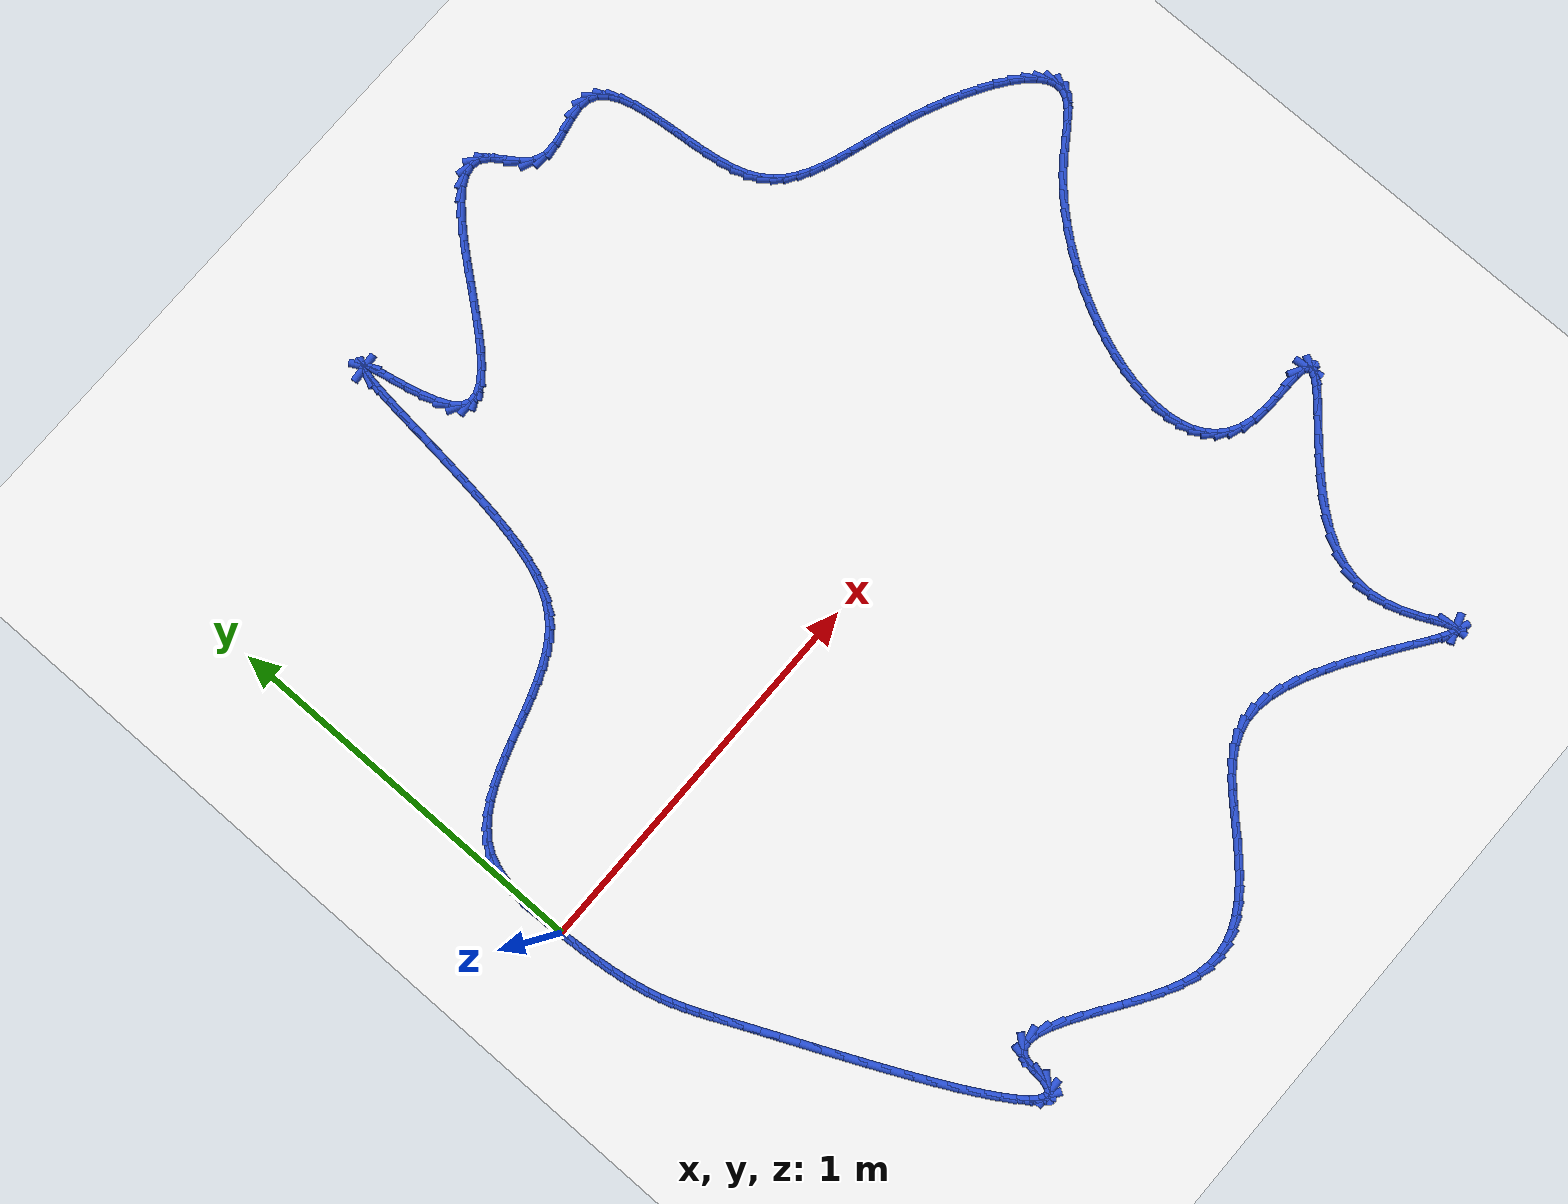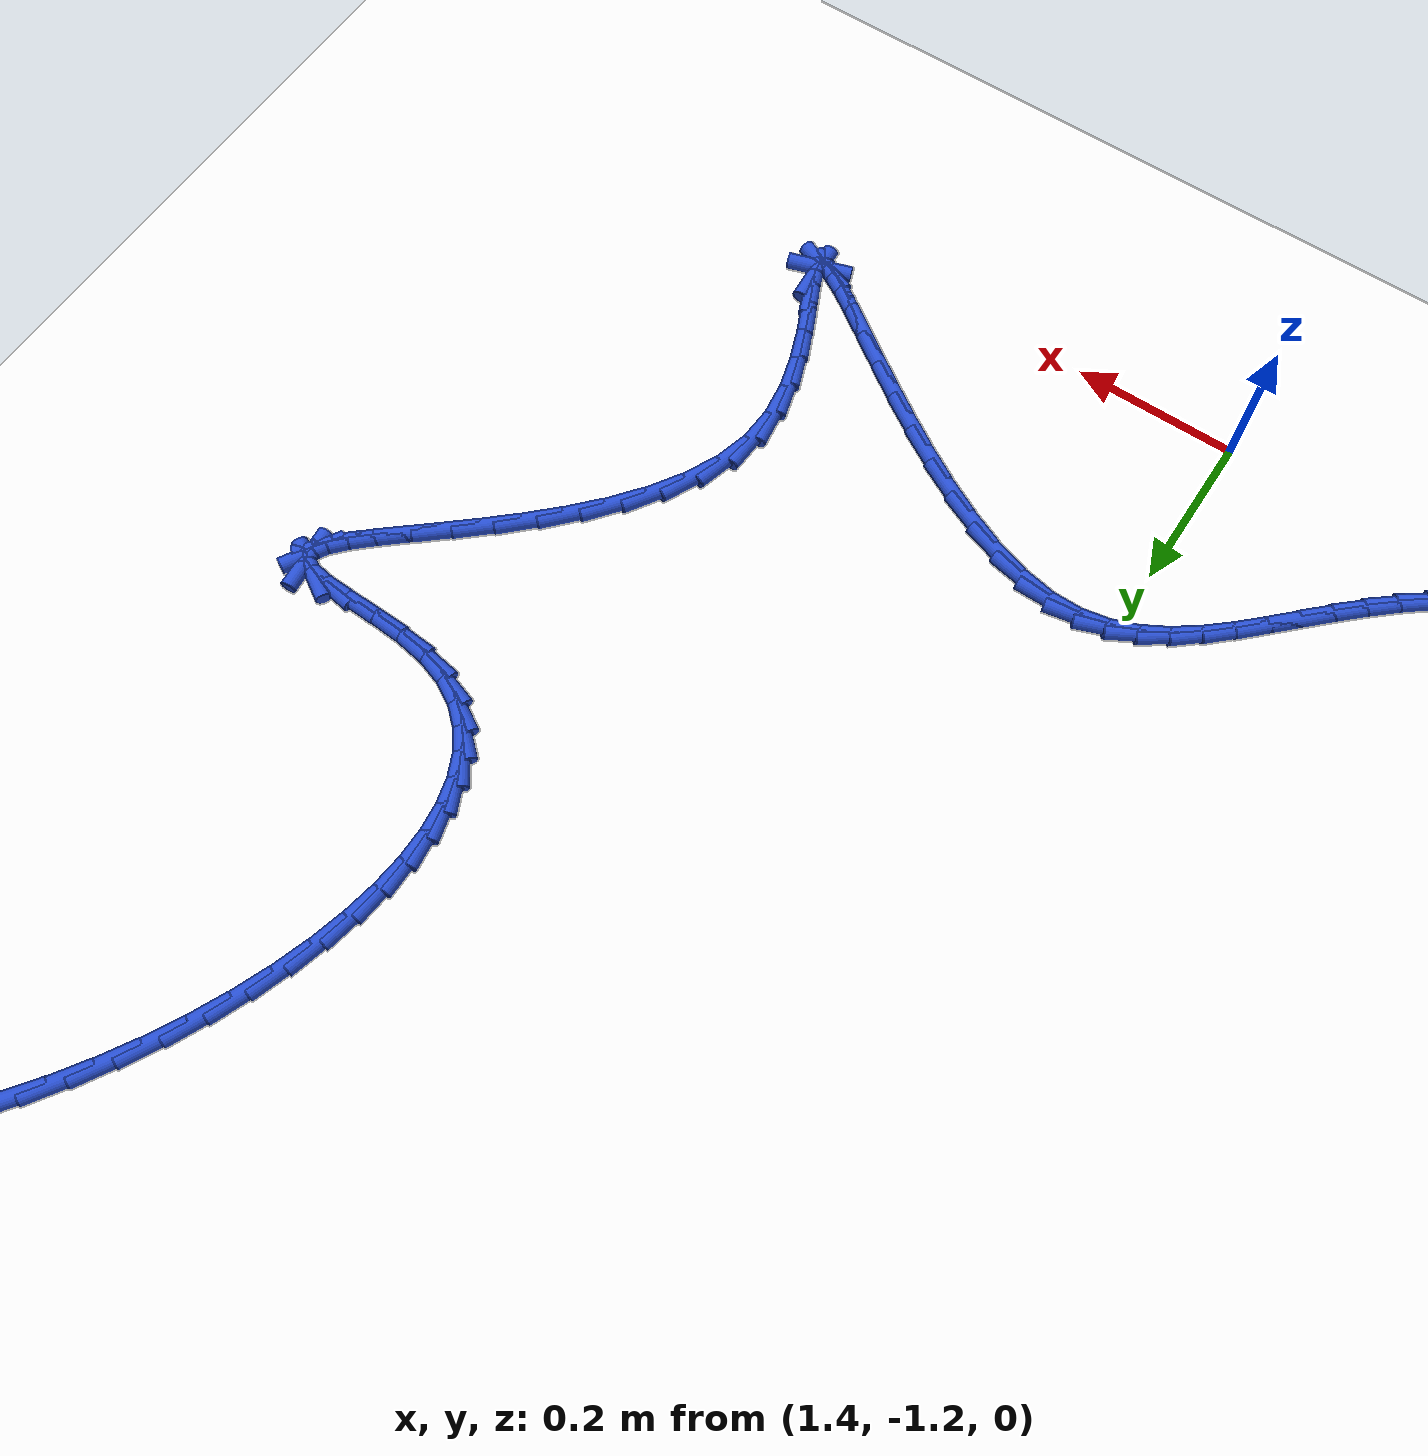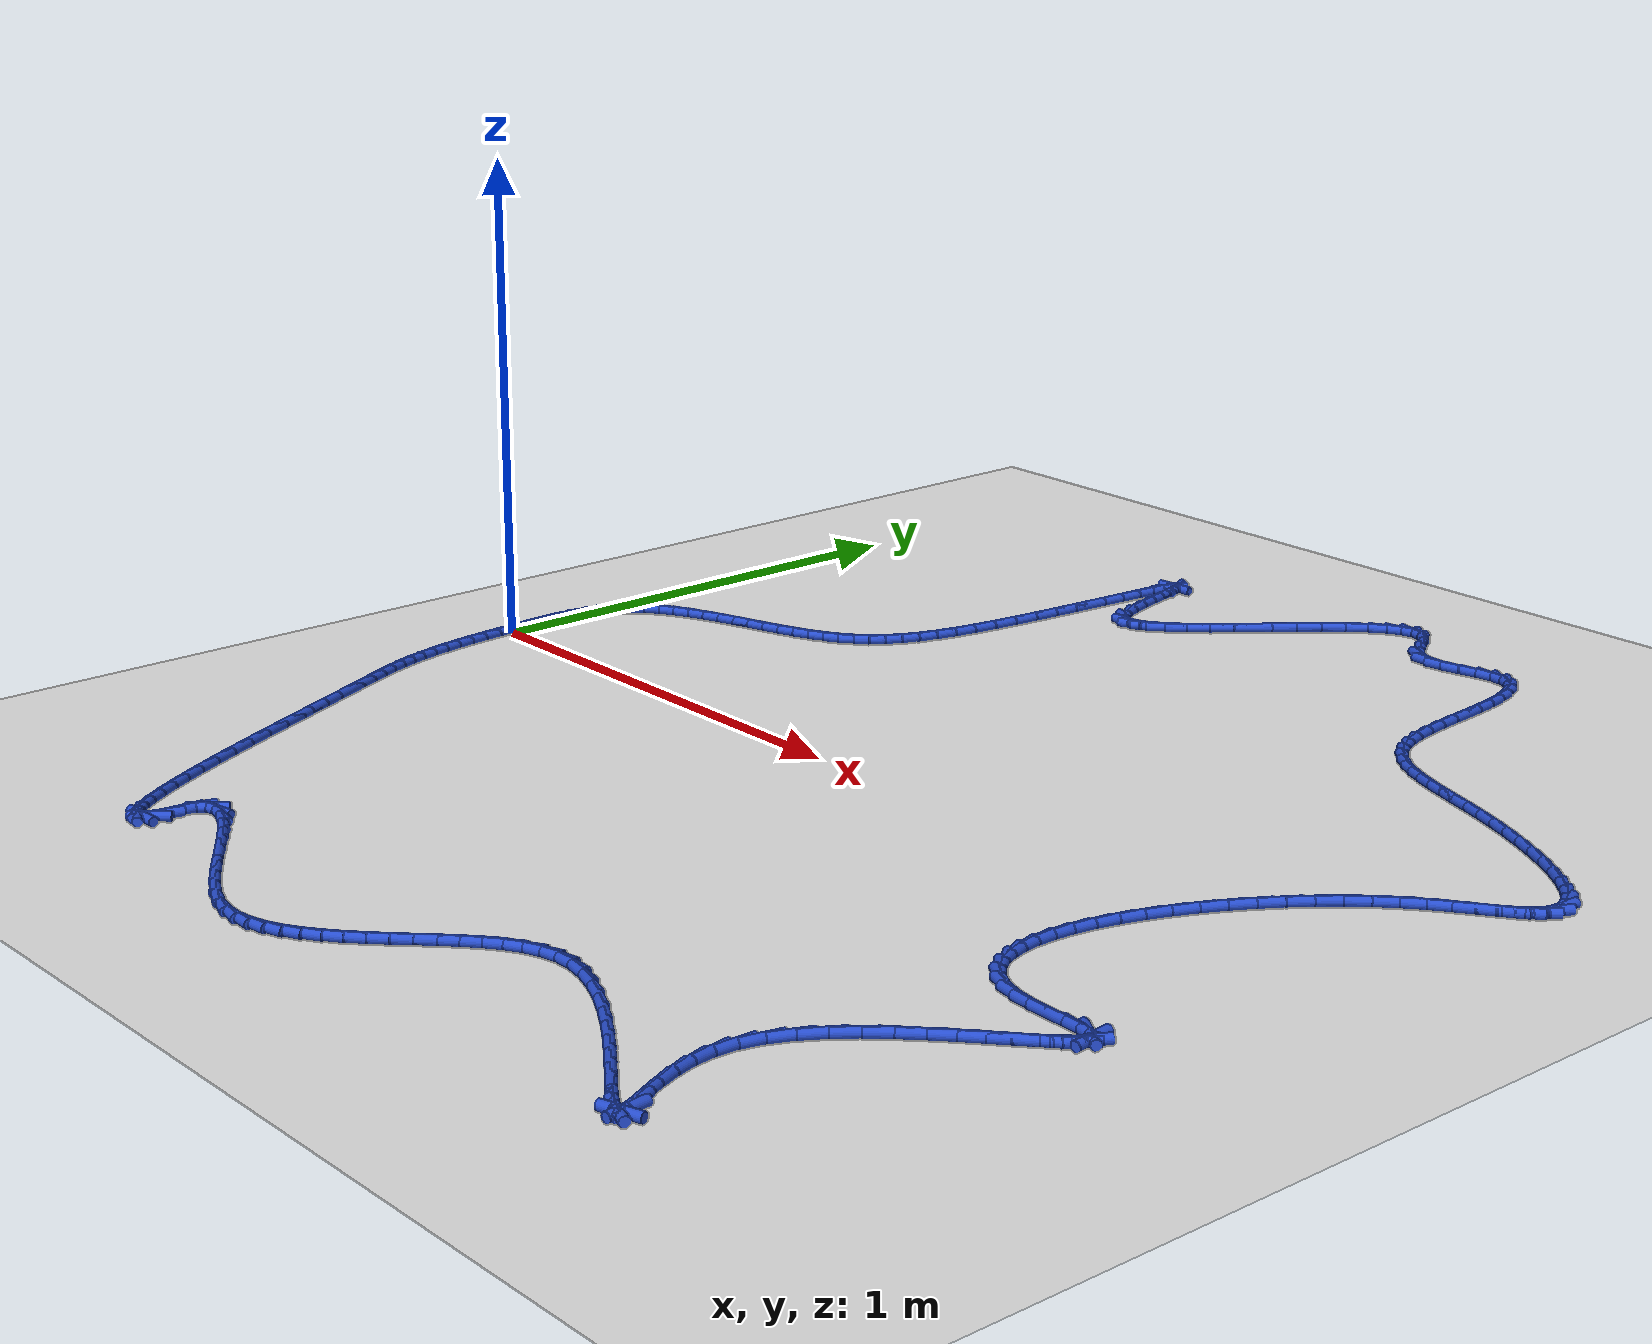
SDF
<sdf version="1.6">
 <world name="default">
  <light name="sun" type="directional">
   <pose>0 0 10 0 -0 0</pose>
   <diffuse>0.8 0.8 0.8 1</diffuse>
   <specular>0.2 0.2 0.2 1</specular>
   <attenuation>
    <range>1000</range>
    <constant>0.9</constant>
    <linear>0.01</linear>
    <quadratic>0.001</quadratic>
   </attenuation>
   <direction>-0.5 0.1 -0.9</direction>
  </light>
  <model name="ground_plane">
   <static>1</static>
   <link name="link">
    <collision name="collision">
     <geometry><plane><normal>0 0 1</normal><size>100 100</size></plane></geometry>
     <surface><friction><ode><mu>100</mu><mu2>50</mu2></ode></friction></surface>
    </collision>
    <visual name="visual">
     <cast_shadows>0</cast_shadows>
     <geometry><plane><normal>0 0 1</normal><size>100 100</size></plane></geometry>
     <material>
      <script><uri>file://media/materials/scripts/gazebo.material</uri><name>Gazebo/WhiteGlow</name></script>
     </material>
    </visual>
   </link>
  </model>
  <gravity>0 0 -9.8</gravity>
  <magnetic_field>6e-06 2.3e-05 -4.2e-05</magnetic_field>
  <atmosphere type="adiabatic"/>
  <physics name="default_physics" default="0" type="ode">
   <max_step_size>0.001</max_step_size>
   <real_time_factor>1</real_time_factor>
   <real_time_update_rate>1000</real_time_update_rate>
  </physics>
  <scene><ambient>0.4 0.4 0.4 1</ambient><background>0.7 0.7 0.7 1</background><shadows>1</shadows></scene>
  <spherical_coordinates>
   <surface_model>EARTH_WGS84</surface_model>
   <latitude_deg>0</latitude_deg>
   <longitude_deg>0</longitude_deg>
   <elevation>0</elevation>
   <heading_deg>0</heading_deg>
  </spherical_coordinates>
  <model name="line">
   <link name="link_0">
    <pose>-2.168404344971009e-18 2.0816681711721685e-17 0.01 0 1.57 -1.5237629214470472</pose>
    <collision name="collision">
     <geometry><cylinder><radius>0.01</radius><length>0.08</length></cylinder></geometry>
    </collision>
    <visual name="visual">
     <material>
      <script><name>Gazebo/Blue</name><uri>file://media/materials/scripts/gazebo.material</uri></script>
     </material>
     <geometry><cylinder><radius>0.01</radius><length>0.08</length></cylinder></geometry>
    </visual>
   </link>
   <link name="link_1">
    <pose>-0.0017802640367481615 0.037823140768470674 0.01 0 1.57 -1.5489615800214063</pose>
    <collision name="collision">
     <geometry><cylinder><radius>0.01</radius><length>0.08</length></cylinder></geometry>
    </collision>
    <visual name="visual">
     <material>
      <script><name>Gazebo/Blue</name><uri>file://media/materials/scripts/gazebo.material</uri></script>
     </material>
     <geometry><cylinder><radius>0.01</radius><length>0.08</length></cylinder></geometry>
    </visual>
   </link>
   <link name="link_2">
    <pose>-0.002605405921722715 0.07560744662147856 0.01 0 1.57 1.5508404619330156</pose>
    <collision name="collision">
     <geometry><cylinder><radius>0.01</radius><length>0.08</length></cylinder></geometry>
    </collision>
    <visual name="visual">
     <material>
      <script><name>Gazebo/Blue</name><uri>file://media/materials/scripts/gazebo.material</uri></script>
     </material>
     <geometry><cylinder><radius>0.01</radius><length>0.08</length></cylinder></geometry>
    </visual>
   </link>
   <link name="link_3">
    <pose>-0.0018631428033497226 0.1127977457538077 0.01 0 1.57 1.4899005535824652</pose>
    <collision name="collision">
     <geometry><cylinder><radius>0.01</radius><length>0.08</length></cylinder></geometry>
    </collision>
    <visual name="visual">
     <material>
      <script><name>Gazebo/Blue</name><uri>file://media/materials/scripts/gazebo.material</uri></script>
     </material>
     <geometry><cylinder><radius>0.01</radius><length>0.08</length></cylinder></geometry>
    </visual>
   </link>
   <link name="link_4">
    <pose>0.0010588081699447506 0.14883886636024216 0.01 0 1.57 1.4058990972291876</pose>
    <collision name="collision">
     <geometry><cylinder><radius>0.01</radius><length>0.08</length></cylinder></geometry>
    </collision>
    <visual name="visual">
     <material>
      <script><name>Gazebo/Blue</name><uri>file://media/materials/scripts/gazebo.material</uri></script>
     </material>
     <geometry><cylinder><radius>0.01</radius><length>0.08</length></cylinder></geometry>
    </visual>
   </link>
   <link name="link_5">
    <pose>0.006772729849734651 0.18317563663556596 0.01 0 1.57 1.293844692095471</pose>
    <collision name="collision">
     <geometry><cylinder><radius>0.01</radius><length>0.08</length></cylinder></geometry>
    </collision>
    <visual name="visual">
     <material>
      <script><name>Gazebo/Blue</name><uri>file://media/materials/scripts/gazebo.material</uri></script>
     </material>
     <geometry><cylinder><radius>0.01</radius><length>0.08</length></cylinder></geometry>
    </visual>
   </link>
   <link name="link_6">
    <pose>0.015890905087593915 0.215252884774563 0.01 0 1.57 1.1488930606979704</pose>
    <collision name="collision">
     <geometry><cylinder><radius>0.01</radius><length>0.08</length></cylinder></geometry>
    </collision>
    <visual name="visual">
     <material>
      <script><name>Gazebo/Blue</name><uri>file://media/materials/scripts/gazebo.material</uri></script>
     </material>
     <geometry><cylinder><radius>0.01</radius><length>0.08</length></cylinder></geometry>
    </visual>
   </link>
   <link name="link_7">
    <pose>0.029025616735096484 0.24451543897201744 0.01 0 1.57 0.9742799033593439</pose>
    <collision name="collision">
     <geometry><cylinder><radius>0.01</radius><length>0.08</length></cylinder></geometry>
    </collision>
    <visual name="visual">
     <material>
      <script><name>Gazebo/Blue</name><uri>file://media/materials/scripts/gazebo.material</uri></script>
     </material>
     <geometry><cylinder><radius>0.01</radius><length>0.08</length></cylinder></geometry>
    </visual>
   </link>
   <link name="link_8">
    <pose>0.04667256238282534 0.27050371364269954 0.01 0 1.57 0.8065654453665723</pose>
    <collision name="collision">
     <geometry><cylinder><radius>0.01</radius><length>0.08</length></cylinder></geometry>
    </collision>
    <visual name="visual">
     <material>
      <script><name>Gazebo/Blue</name><uri>file://media/materials/scripts/gazebo.material</uri></script>
     </material>
     <geometry><cylinder><radius>0.01</radius><length>0.08</length></cylinder></geometry>
    </visual>
   </link>
   <link name="link_9">
    <pose>0.06858651710284266 0.2933655926383066 0.01 0 1.57 0.6652715669156853</pose>
    <collision name="collision">
     <geometry><cylinder><radius>0.01</radius><length>0.08</length></cylinder></geometry>
    </collision>
    <visual name="visual">
     <material>
      <script><name>Gazebo/Blue</name><uri>file://media/materials/scripts/gazebo.material</uri></script>
     </material>
     <geometry><cylinder><radius>0.01</radius><length>0.08</length></cylinder></geometry>
    </visual>
   </link>
   <link name="link_10">
    <pose>0.09423215118579009 0.3134868116557885 0.01 0 1.57 0.5521163759444384</pose>
    <collision name="collision">
     <geometry><cylinder><radius>0.01</radius><length>0.08</length></cylinder></geometry>
    </collision>
    <visual name="visual">
     <material>
      <script><name>Gazebo/Blue</name><uri>file://media/materials/scripts/gazebo.material</uri></script>
     </material>
     <geometry><cylinder><radius>0.01</radius><length>0.08</length></cylinder></geometry>
    </visual>
   </link>
   <link name="link_11">
    <pose>0.12307345899037024 0.33125366057689043 0.01 0 1.57 0.46487299728538056</pose>
    <collision name="collision">
     <geometry><cylinder><radius>0.01</radius><length>0.08</length></cylinder></geometry>
    </collision>
    <visual name="visual">
     <material>
      <script><name>Gazebo/Blue</name><uri>file://media/materials/scripts/gazebo.material</uri></script>
     </material>
     <geometry><cylinder><radius>0.01</radius><length>0.08</length></cylinder></geometry>
    </visual>
   </link>
   <link name="link_12">
    <pose>0.15457443487528585 0.34705242928335783 0.01 0 1.57 0.4000178957762174</pose>
    <collision name="collision">
     <geometry><cylinder><radius>0.01</radius><length>0.08</length></cylinder></geometry>
    </collision>
    <visual name="visual">
     <material>
      <script><name>Gazebo/Blue</name><uri>file://media/materials/scripts/gazebo.material</uri></script>
     </material>
     <geometry><cylinder><radius>0.01</radius><length>0.08</length></cylinder></geometry>
    </visual>
   </link>
   <link name="link_13">
    <pose>0.18819907319923954 0.3612694076569358 0.01 0 1.57 0.35420327086516223</pose>
    <collision name="collision">
     <geometry><cylinder><radius>0.01</radius><length>0.08</length></cylinder></geometry>
    </collision>
    <visual name="visual">
     <material>
      <script><name>Gazebo/Blue</name><uri>file://media/materials/scripts/gazebo.material</uri></script>
     </material>
     <geometry><cylinder><radius>0.01</radius><length>0.08</length></cylinder></geometry>
    </visual>
   </link>
   <link name="link_14">
    <pose>0.22341136832093392 0.37429088557936985 0.01 0 1.57 0.3248318928129219</pose>
    <collision name="collision">
     <geometry><cylinder><radius>0.01</radius><length>0.08</length></cylinder></geometry>
    </collision>
    <visual name="visual">
     <material>
      <script><name>Gazebo/Blue</name><uri>file://media/materials/scripts/gazebo.material</uri></script>
     </material>
     <geometry><cylinder><radius>0.01</radius><length>0.08</length></cylinder></geometry>
    </visual>
   </link>
   <link name="link_15">
    <pose>0.25967531459907156 0.38650315293240517 0.01 0 1.57 0.31019311026481466</pose>
    <collision name="collision">
     <geometry><cylinder><radius>0.01</radius><length>0.08</length></cylinder></geometry>
    </collision>
    <visual name="visual">
     <material>
      <script><name>Gazebo/Blue</name><uri>file://media/materials/scripts/gazebo.material</uri></script>
     </material>
     <geometry><cylinder><radius>0.01</radius><length>0.08</length></cylinder></geometry>
    </visual>
   </link>
   <link name="link_16">
    <pose>0.2964549063923554 0.3982924995977871 0.01 0 1.57 0.30945027306328715</pose>
    <collision name="collision">
     <geometry><cylinder><radius>0.01</radius><length>0.08</length></cylinder></geometry>
    </collision>
    <visual name="visual">
     <material>
      <script><name>Gazebo/Blue</name><uri>file://media/materials/scripts/gazebo.material</uri></script>
     </material>
     <geometry><cylinder><radius>0.01</radius><length>0.08</length></cylinder></geometry>
    </visual>
   </link>
   <link name="link_17">
    <pose>0.33321413805948785 0.410045215457261 0.01 0 1.57 0.3226142611338863</pose>
    <collision name="collision">
     <geometry><cylinder><radius>0.01</radius><length>0.08</length></cylinder></geometry>
    </collision>
    <visual name="visual">
     <material>
      <script><name>Gazebo/Blue</name><uri>file://media/materials/scripts/gazebo.material</uri></script>
     </material>
     <geometry><cylinder><radius>0.01</radius><length>0.08</length></cylinder></geometry>
    </visual>
   </link>
   <link name="link_18">
    <pose>0.36941700395917165 0.42214759039257194 0.01 0 1.57 0.3505526300368972</pose>
    <collision name="collision">
     <geometry><cylinder><radius>0.01</radius><length>0.08</length></cylinder></geometry>
    </collision>
    <visual name="visual">
     <material>
      <script><name>Gazebo/Blue</name><uri>file://media/materials/scripts/gazebo.material</uri></script>
     </material>
     <geometry><cylinder><radius>0.01</radius><length>0.08</length></cylinder></geometry>
    </visual>
   </link>
   <link name="link_19">
    <pose>0.4045274984501094 0.4349859142854655 0.01 0 1.57 0.3950374481154847</pose>
    <collision name="collision">
     <geometry><cylinder><radius>0.01</radius><length>0.08</length></cylinder></geometry>
    </collision>
    <visual name="visual">
     <material>
      <script><name>Gazebo/Blue</name><uri>file://media/materials/scripts/gazebo.material</uri></script>
     </material>
     <geometry><cylinder><radius>0.01</radius><length>0.08</length></cylinder></geometry>
    </visual>
   </link>
   <link name="link_20">
    <pose>0.4380096158910036 0.4489464770176867 0.01 0 1.57 0.4587881123124792</pose>
    <collision name="collision">
     <geometry><cylinder><radius>0.01</radius><length>0.08</length></cylinder></geometry>
    </collision>
    <visual name="visual">
     <material>
      <script><name>Gazebo/Blue</name><uri>file://media/materials/scripts/gazebo.material</uri></script>
     </material>
     <geometry><cylinder><radius>0.01</radius><length>0.08</length></cylinder></geometry>
    </visual>
   </link>
   <link name="link_21">
    <pose>0.4693273506405574 0.4644155684709812 0.01 0 1.57 0.5453765180381601</pose>
    <collision name="collision">
     <geometry><cylinder><radius>0.01</radius><length>0.08</length></cylinder></geometry>
    </collision>
    <visual name="visual">
     <material>
      <script><name>Gazebo/Blue</name><uri>file://media/materials/scripts/gazebo.material</uri></script>
     </material>
     <geometry><cylinder><radius>0.01</radius><length>0.08</length></cylinder></geometry>
    </visual>
   </link>
   <link name="link_22">
    <pose>0.497944697057473 0.481779478527094 0.01 0 1.57 0.6579175670772536</pose>
    <collision name="collision">
     <geometry><cylinder><radius>0.01</radius><length>0.08</length></cylinder></geometry>
    </collision>
    <visual name="visual">
     <material>
      <script><name>Gazebo/Blue</name><uri>file://media/materials/scripts/gazebo.material</uri></script>
     </material>
     <geometry><cylinder><radius>0.01</radius><length>0.08</length></cylinder></geometry>
    </visual>
   </link>
   <link name="link_23">
    <pose>0.5233579617456157 0.5014181767640815 0.01 0 1.57 0.7860877448354555</pose>
    <collision name="collision">
     <geometry><cylinder><radius>0.01</radius><length>0.08</length></cylinder></geometry>
    </collision>
    <visual name="visual">
     <material>
      <script><name>Gazebo/Blue</name><uri>file://media/materials/scripts/gazebo.material</uri></script>
     </material>
     <geometry><cylinder><radius>0.01</radius><length>0.08</length></cylinder></geometry>
    </visual>
   </link>
   <link name="link_24">
    <pose>0.5455296327823708 0.5236204472520936 0.01 0 1.57 0.9145304912818619</pose>
    <collision name="collision">
     <geometry><cylinder><radius>0.01</radius><length>0.08</length></cylinder></geometry>
    </collision>
    <visual name="visual">
     <material>
      <script><name>Gazebo/Blue</name><uri>file://media/materials/scripts/gazebo.material</uri></script>
     </material>
     <geometry><cylinder><radius>0.01</radius><length>0.08</length></cylinder></geometry>
    </visual>
   </link>
   <link name="link_25">
    <pose>0.5647724157699903 0.5486065712041363 0.01 0 1.57 1.0345388438335907</pose>
    <collision name="collision">
     <geometry><cylinder><radius>0.01</radius><length>0.08</length></cylinder></geometry>
    </collision>
    <visual name="visual">
     <material>
      <script><name>Gazebo/Blue</name><uri>file://media/materials/scripts/gazebo.material</uri></script>
     </material>
     <geometry><cylinder><radius>0.01</radius><length>0.08</length></cylinder></geometry>
    </visual>
   </link>
   <link name="link_26">
    <pose>0.5814075393596708 0.5765951627173169 0.01 0 1.57 1.1398627381804094</pose>
    <collision name="collision">
     <geometry><cylinder><radius>0.01</radius><length>0.08</length></cylinder></geometry>
    </collision>
    <visual name="visual">
     <material>
      <script><name>Gazebo/Blue</name><uri>file://media/materials/scripts/gazebo.material</uri></script>
     </material>
     <geometry><cylinder><radius>0.01</radius><length>0.08</length></cylinder></geometry>
    </visual>
   </link>
   <link name="link_27">
    <pose>0.595756232202608 0.607804835888742 0.01 0 1.57 1.227549307937443</pose>
    <collision name="collision">
     <geometry><cylinder><radius>0.01</radius><length>0.08</length></cylinder></geometry>
    </collision>
    <visual name="visual">
     <material>
      <script><name>Gazebo/Blue</name><uri>file://media/materials/scripts/gazebo.material</uri></script>
     </material>
     <geometry><cylinder><radius>0.01</radius><length>0.08</length></cylinder></geometry>
    </visual>
   </link>
   <link name="link_28">
    <pose>0.6081397229499977 0.6424542048155183 0.01 0 1.57 1.297464077118905</pose>
    <collision name="collision">
     <geometry><cylinder><radius>0.01</radius><length>0.08</length></cylinder></geometry>
    </collision>
    <visual name="visual">
     <material>
      <script><name>Gazebo/Blue</name><uri>file://media/materials/scripts/gazebo.material</uri></script>
     </material>
     <geometry><cylinder><radius>0.01</radius><length>0.08</length></cylinder></geometry>
    </visual>
   </link>
   <link name="link_29">
    <pose>0.6188792402530364 0.6807618835947528 0.01 0 1.57 1.351169408942097</pose>
    <collision name="collision">
     <geometry><cylinder><radius>0.01</radius><length>0.08</length></cylinder></geometry>
    </collision>
    <visual name="visual">
     <material>
      <script><name>Gazebo/Blue</name><uri>file://media/materials/scripts/gazebo.material</uri></script>
     </material>
     <geometry><cylinder><radius>0.01</radius><length>0.08</length></cylinder></geometry>
    </visual>
   </link>
   <link name="link_30">
    <pose>0.6282960127629196 0.7229464863235519 0.01 0 1.57 1.3909107061222115</pose>
    <collision name="collision">
     <geometry><cylinder><radius>0.01</radius><length>0.08</length></cylinder></geometry>
    </collision>
    <visual name="visual">
     <material>
      <script><name>Gazebo/Blue</name><uri>file://media/materials/scripts/gazebo.material</uri></script>
     </material>
     <geometry><cylinder><radius>0.01</radius><length>0.08</length></cylinder></geometry>
    </visual>
   </link>
   <link name="link_31">
    <pose>0.6367041498422326 0.7691828018516689 0.01 0 1.57 1.4192503464533055</pose>
    <collision name="collision">
     <geometry><cylinder><radius>0.01</radius><length>0.08</length></cylinder></geometry>
    </collision>
    <visual name="visual">
     <material>
      <script><name>Gazebo/Blue</name><uri>file://media/materials/scripts/gazebo.material</uri></script>
     </material>
     <geometry><cylinder><radius>0.01</radius><length>0.08</length></cylinder></geometry>
    </visual>
   </link>
   <link name="link_32">
    <pose>0.6442994453411758 0.8189172869047909 0.01 0 1.57 1.4394356341061534</pose>
    <collision name="collision">
     <geometry><cylinder><radius>0.01</radius><length>0.08</length></cylinder></geometry>
    </collision>
    <visual name="visual">
     <material>
      <script><name>Gazebo/Blue</name><uri>file://media/materials/scripts/gazebo.material</uri></script>
     </material>
     <geometry><cylinder><radius>0.01</radius><length>0.08</length></cylinder></geometry>
    </visual>
   </link>
   <link name="link_33">
    <pose>0.6511801800050763 0.870996122510461 0.01 0 1.57 1.4537493055079098</pose>
    <collision name="collision">
     <geometry><cylinder><radius>0.01</radius><length>0.08</length></cylinder></geometry>
    </collision>
    <visual name="visual">
     <material>
      <script><name>Gazebo/Blue</name><uri>file://media/materials/scripts/gazebo.material</uri></script>
     </material>
     <geometry><cylinder><radius>0.01</radius><length>0.08</length></cylinder></geometry>
    </visual>
   </link>
   <link name="link_34">
    <pose>0.657441724599184 0.9242475763057676 0.01 0 1.57 1.4634644187524293</pose>
    <collision name="collision">
     <geometry><cylinder><radius>0.01</radius><length>0.08</length></cylinder></geometry>
    </collision>
    <visual name="visual">
     <material>
      <script><name>Gazebo/Blue</name><uri>file://media/materials/scripts/gazebo.material</uri></script>
     </material>
     <geometry><cylinder><radius>0.01</radius><length>0.08</length></cylinder></geometry>
    </visual>
   </link>
   <link name="link_35">
    <pose>0.6631794498887498 0.9774999159278012 0.01 0 1.57 1.4692055556160488</pose>
    <collision name="collision">
     <geometry><cylinder><radius>0.01</radius><length>0.08</length></cylinder></geometry>
    </collision>
    <visual name="visual">
     <material>
      <script><name>Gazebo/Blue</name><uri>file://media/materials/scripts/gazebo.material</uri></script>
     </material>
     <geometry><cylinder><radius>0.01</radius><length>0.08</length></cylinder></geometry>
    </visual>
   </link>
   <link name="link_36">
    <pose>0.6684887266390234 1.0295814090136501 0.01 0 1.57 1.4710817404510814</pose>
    <collision name="collision">
     <geometry><cylinder><radius>0.01</radius><length>0.08</length></cylinder></geometry>
    </collision>
    <visual name="visual">
     <material>
      <script><name>Gazebo/Blue</name><uri>file://media/materials/scripts/gazebo.material</uri></script>
     </material>
     <geometry><cylinder><radius>0.01</radius><length>0.08</length></cylinder></geometry>
    </visual>
   </link>
   <link name="link_37">
    <pose>0.6734649256152548 1.0793203232004043 0.01 0 1.57 1.4686429787536295</pose>
    <collision name="collision">
     <geometry><cylinder><radius>0.01</radius><length>0.08</length></cylinder></geometry>
    </collision>
    <visual name="visual">
     <material>
      <script><name>Gazebo/Blue</name><uri>file://media/materials/scripts/gazebo.material</uri></script>
     </material>
     <geometry><cylinder><radius>0.01</radius><length>0.08</length></cylinder></geometry>
    </visual>
   </link>
   <link name="link_38">
    <pose>0.678203417582695 1.1255449261251536 0.01 0 1.57 1.4605966585047636</pose>
    <collision name="collision">
     <geometry><cylinder><radius>0.01</radius><length>0.08</length></cylinder></geometry>
    </collision>
    <visual name="visual">
     <material>
      <script><name>Gazebo/Blue</name><uri>file://media/materials/scripts/gazebo.material</uri></script>
     </material>
     <geometry><cylinder><radius>0.01</radius><length>0.08</length></cylinder></geometry>
    </visual>
   </link>
   <link name="link_39">
    <pose>0.6827995733065937 1.1670834854249863 0.01 0 1.57 1.4439835792000386</pose>
    <collision name="collision">
     <geometry><cylinder><radius>0.01</radius><length>0.08</length></cylinder></geometry>
    </collision>
    <visual name="visual">
     <material>
      <script><name>Gazebo/Blue</name><uri>file://media/materials/scripts/gazebo.material</uri></script>
     </material>
     <geometry><cylinder><radius>0.01</radius><length>0.08</length></cylinder></geometry>
    </visual>
   </link>
   <link name="link_40">
    <pose>0.6873487635522011 1.2027642687369928 0.01 0 1.57 1.4116853669240994</pose>
    <collision name="collision">
     <geometry><cylinder><radius>0.01</radius><length>0.08</length></cylinder></geometry>
    </collision>
    <visual name="visual">
     <material>
      <script><name>Gazebo/Blue</name><uri>file://media/materials/scripts/gazebo.material</uri></script>
     </material>
     <geometry><cylinder><radius>0.01</radius><length>0.08</length></cylinder></geometry>
    </visual>
   </link>
   <link name="link_41">
    <pose>0.6919463590847681 1.2314155436982623 0.01 0 1.57 1.3429701531673195</pose>
    <collision name="collision">
     <geometry><cylinder><radius>0.01</radius><length>0.08</length></cylinder></geometry>
    </collision>
    <visual name="visual">
     <material>
      <script><name>Gazebo/Blue</name><uri>file://media/materials/scripts/gazebo.material</uri></script>
     </material>
     <geometry><cylinder><radius>0.01</radius><length>0.08</length></cylinder></geometry>
    </visual>
   </link>
   <link name="link_42">
    <pose>0.696687730669544 1.2518655779458836 0.01 0 1.57 1.1482546872405694</pose>
    <collision name="collision">
     <geometry><cylinder><radius>0.01</radius><length>0.08</length></cylinder></geometry>
    </collision>
    <visual name="visual">
     <material>
      <script><name>Gazebo/Blue</name><uri>file://media/materials/scripts/gazebo.material</uri></script>
     </material>
     <geometry><cylinder><radius>0.01</radius><length>0.08</length></cylinder></geometry>
    </visual>
   </link>
   <link name="link_43">
    <pose>0.7016682490717798 1.2629426391169467 0.01 0 1.57 0.09982738758546614</pose>
    <collision name="collision">
     <geometry><cylinder><radius>0.01</radius><length>0.08</length></cylinder></geometry>
    </collision>
    <visual name="visual">
     <material>
      <script><name>Gazebo/Blue</name><uri>file://media/materials/scripts/gazebo.material</uri></script>
     </material>
     <geometry><cylinder><radius>0.01</radius><length>0.08</length></cylinder></geometry>
    </visual>
   </link>
   <link name="link_44">
    <pose>0.7069832850567251 1.2634749948485404 0.01 0 1.57 -1.096272839131088</pose>
    <collision name="collision">
     <geometry><cylinder><radius>0.01</radius><length>0.08</length></cylinder></geometry>
    </collision>
    <visual name="visual">
     <material>
      <script><name>Gazebo/Blue</name><uri>file://media/materials/scripts/gazebo.material</uri></script>
     </material>
     <geometry><cylinder><radius>0.01</radius><length>0.08</length></cylinder></geometry>
    </visual>
   </link>
   <link name="link_45">
    <pose>0.7127282093896309 1.252290912777755 0.01 0 1.57 -1.3085836102659933</pose>
    <collision name="collision">
     <geometry><cylinder><radius>0.01</radius><length>0.08</length></cylinder></geometry>
    </collision>
    <visual name="visual">
     <material>
      <script><name>Gazebo/Blue</name><uri>file://media/materials/scripts/gazebo.material</uri></script>
     </material>
     <geometry><cylinder><radius>0.01</radius><length>0.08</length></cylinder></geometry>
    </visual>
   </link>
   <link name="link_46">
    <pose>0.7190306363501431 1.2288087628413726 0.01 0 1.57 -1.357377585973937</pose>
    <collision name="collision">
     <geometry><cylinder><radius>0.01</radius><length>0.08</length></cylinder></geometry>
    </collision>
    <visual name="visual">
     <material>
      <script><name>Gazebo/Blue</name><uri>file://media/materials/scripts/gazebo.material</uri></script>
     </material>
     <geometry><cylinder><radius>0.01</radius><length>0.08</length></cylinder></geometry>
    </visual>
   </link>
   <link name="link_47">
    <pose>0.72619794569816 1.19573687964935 0.01 0 1.57 -1.3576183703244797</pose>
    <collision name="collision">
     <geometry><cylinder><radius>0.01</radius><length>0.08</length></cylinder></geometry>
    </collision>
    <visual name="visual">
     <material>
      <script><name>Gazebo/Blue</name><uri>file://media/materials/scripts/gazebo.material</uri></script>
     </material>
     <geometry><cylinder><radius>0.01</radius><length>0.08</length></cylinder></geometry>
    </visual>
   </link>
   <link name="link_48">
    <pose>0.7345997942027793 1.156923355900513 0.01 0 1.57 -1.3297610556954285</pose>
    <collision name="collision">
     <geometry><cylinder><radius>0.01</radius><length>0.08</length></cylinder></geometry>
    </collision>
    <visual name="visual">
     <material>
      <script><name>Gazebo/Blue</name><uri>file://media/materials/scripts/gazebo.material</uri></script>
     </material>
     <geometry><cylinder><radius>0.01</radius><length>0.08</length></cylinder></geometry>
    </visual>
   </link>
   <link name="link_49">
    <pose>0.7446058993520535 1.1162173955371593 0.01 0 1.57 -1.2709482701935573</pose>
    <collision name="collision">
     <geometry><cylinder><radius>0.01</radius><length>0.08</length></cylinder></geometry>
    </collision>
    <visual name="visual">
     <material>
      <script><name>Gazebo/Blue</name><uri>file://media/materials/scripts/gazebo.material</uri></script>
     </material>
     <geometry><cylinder><radius>0.01</radius><length>0.08</length></cylinder></geometry>
    </visual>
   </link>
   <link name="link_50">
    <pose>0.7565859786340348 1.0774682025015858 0.01 0 1.57 -1.1606528772561064</pose>
    <collision name="collision">
     <geometry><cylinder><radius>0.01</radius><length>0.08</length></cylinder></geometry>
    </collision>
    <visual name="visual">
     <material>
      <script><name>Gazebo/Blue</name><uri>file://media/materials/scripts/gazebo.material</uri></script>
     </material>
     <geometry><cylinder><radius>0.01</radius><length>0.08</length></cylinder></geometry>
    </visual>
   </link>
   <link name="link_51">
    <pose>0.7709097495367757 1.0445249807360906 0.01 0 1.57 -0.9391876550288493</pose>
    <collision name="collision">
     <geometry><cylinder><radius>0.01</radius><length>0.08</length></cylinder></geometry>
    </collision>
    <visual name="visual">
     <material>
      <script><name>Gazebo/Blue</name><uri>file://media/materials/scripts/gazebo.material</uri></script>
     </material>
     <geometry><cylinder><radius>0.01</radius><length>0.08</length></cylinder></geometry>
    </visual>
   </link>
   <link name="link_52">
    <pose>0.7879469180049615 1.0212368454535667 0.01 0 1.57 -0.4957348741669882</pose>
    <collision name="collision">
     <geometry><cylinder><radius>0.01</radius><length>0.08</length></cylinder></geometry>
    </collision>
    <visual name="visual">
     <material>
      <script><name>Gazebo/Blue</name><uri>file://media/materials/scripts/gazebo.material</uri></script>
     </material>
     <geometry><cylinder><radius>0.01</radius><length>0.08</length></cylinder></geometry>
    </visual>
   </link>
   <link name="link_53">
    <pose>0.8079338971057203 1.0104283410003894 0.01 0 1.57 0.04082333624782419</pose>
    <collision name="collision">
     <geometry><cylinder><radius>0.01</radius><length>0.08</length></cylinder></geometry>
    </collision>
    <visual name="visual">
     <material>
      <script><name>Gazebo/Blue</name><uri>file://media/materials/scripts/gazebo.material</uri></script>
     </material>
     <geometry><cylinder><radius>0.01</radius><length>0.08</length></cylinder></geometry>
    </visual>
   </link>
   <link name="link_54">
    <pose>0.8306429035655808 1.0113559137447183 0.01 0 1.57 0.4178014793891592</pose>
    <collision name="collision">
     <geometry><cylinder><radius>0.01</radius><length>0.08</length></cylinder></geometry>
    </collision>
    <visual name="visual">
     <material>
      <script><name>Gazebo/Blue</name><uri>file://media/materials/scripts/gazebo.material</uri></script>
     </material>
     <geometry><cylinder><radius>0.01</radius><length>0.08</length></cylinder></geometry>
    </visual>
   </link>
   <link name="link_55">
    <pose>0.855745167736445 1.0224997667981106 0.01 0 1.57 0.6307844151344876</pose>
    <collision name="collision">
     <geometry><cylinder><radius>0.01</radius><length>0.08</length></cylinder></geometry>
    </collision>
    <visual name="visual">
     <material>
      <script><name>Gazebo/Blue</name><uri>file://media/materials/scripts/gazebo.material</uri></script>
     </material>
     <geometry><cylinder><radius>0.01</radius><length>0.08</length></cylinder></geometry>
    </visual>
   </link>
   <link name="link_56">
    <pose>0.8829119199702158 1.0423401032721245 0.01 0 1.57 0.751693751628106</pose>
    <collision name="collision">
     <geometry><cylinder><radius>0.01</radius><length>0.08</length></cylinder></geometry>
    </collision>
    <visual name="visual">
     <material>
      <script><name>Gazebo/Blue</name><uri>file://media/materials/scripts/gazebo.material</uri></script>
     </material>
     <geometry><cylinder><radius>0.01</radius><length>0.08</length></cylinder></geometry>
    </visual>
   </link>
   <link name="link_57">
    <pose>0.9118143906187954 1.0693571262783177 0.01 0 1.57 0.8229221126805729</pose>
    <collision name="collision">
     <geometry><cylinder><radius>0.01</radius><length>0.08</length></cylinder></geometry>
    </collision>
    <visual name="visual">
     <material>
      <script><name>Gazebo/Blue</name><uri>file://media/materials/scripts/gazebo.material</uri></script>
     </material>
     <geometry><cylinder><radius>0.01</radius><length>0.08</length></cylinder></geometry>
    </visual>
   </link>
   <link name="link_58">
    <pose>0.9421238100340865 1.1020310389282482 0.01 0 1.57 0.8647548827633805</pose>
    <collision name="collision">
     <geometry><cylinder><radius>0.01</radius><length>0.08</length></cylinder></geometry>
    </collision>
    <visual name="visual">
     <material>
      <script><name>Gazebo/Blue</name><uri>file://media/materials/scripts/gazebo.material</uri></script>
     </material>
     <geometry><cylinder><radius>0.01</radius><length>0.08</length></cylinder></geometry>
    </visual>
   </link>
   <link name="link_59">
    <pose>0.9735114085679918 1.138842044333473 0.01 0 1.57 0.8869308898965139</pose>
    <collision name="collision">
     <geometry><cylinder><radius>0.01</radius><length>0.08</length></cylinder></geometry>
    </collision>
    <visual name="visual">
     <material>
      <script><name>Gazebo/Blue</name><uri>file://media/materials/scripts/gazebo.material</uri></script>
     </material>
     <geometry><cylinder><radius>0.01</radius><length>0.08</length></cylinder></geometry>
    </visual>
   </link>
   <link name="link_60">
    <pose>1.0056484165724136 1.1782703456055506 0.01 0 1.57 0.8939973481487795</pose>
    <collision name="collision">
     <geometry><cylinder><radius>0.01</radius><length>0.08</length></cylinder></geometry>
    </collision>
    <visual name="visual">
     <material>
      <script><name>Gazebo/Blue</name><uri>file://media/materials/scripts/gazebo.material</uri></script>
     </material>
     <geometry><cylinder><radius>0.01</radius><length>0.08</length></cylinder></geometry>
    </visual>
   </link>
   <link name="link_61">
    <pose>1.0382060643992546 1.218796145856039 0.01 0 1.57 0.8874979151706106</pose>
    <collision name="collision">
     <geometry><cylinder><radius>0.01</radius><length>0.08</length></cylinder></geometry>
    </collision>
    <visual name="visual">
     <material>
      <script><name>Gazebo/Blue</name><uri>file://media/materials/scripts/gazebo.material</uri></script>
     </material>
     <geometry><cylinder><radius>0.01</radius><length>0.08</length></cylinder></geometry>
    </visual>
   </link>
   <link name="link_62">
    <pose>1.0708555824004167 1.2588996481964951 0.01 0 1.57 0.8666762860536887</pose>
    <collision name="collision">
     <geometry><cylinder><radius>0.01</radius><length>0.08</length></cylinder></geometry>
    </collision>
    <visual name="visual">
     <material>
      <script><name>Gazebo/Blue</name><uri>file://media/materials/scripts/gazebo.material</uri></script>
     </material>
     <geometry><cylinder><radius>0.01</radius><length>0.08</length></cylinder></geometry>
    </visual>
   </link>
   <link name="link_63">
    <pose>1.1032682009278036 1.2970610557384776 0.01 0 1.57 0.8282377220193725</pose>
    <collision name="collision">
     <geometry><cylinder><radius>0.01</radius><length>0.08</length></cylinder></geometry>
    </collision>
    <visual name="visual">
     <material>
      <script><name>Gazebo/Blue</name><uri>file://media/materials/scripts/gazebo.material</uri></script>
     </material>
     <geometry><cylinder><radius>0.01</radius><length>0.08</length></cylinder></geometry>
    </visual>
   </link>
   <link name="link_64">
    <pose>1.1351151503333172 1.3317605715935439 0.01 0 1.57 0.7650502801931045</pose>
    <collision name="collision">
     <geometry><cylinder><radius>0.01</radius><length>0.08</length></cylinder></geometry>
    </collision>
    <visual name="visual">
     <material>
      <script><name>Gazebo/Blue</name><uri>file://media/materials/scripts/gazebo.material</uri></script>
     </material>
     <geometry><cylinder><radius>0.01</radius><length>0.08</length></cylinder></geometry>
    </visual>
   </link>
   <link name="link_65">
    <pose>1.16606766096886 1.3614783988732517 0.01 0 1.57 0.6630008591409428</pose>
    <collision name="collision">
     <geometry><cylinder><radius>0.01</radius><length>0.08</length></cylinder></geometry>
    </collision>
    <visual name="visual">
     <material>
      <script><name>Gazebo/Blue</name><uri>file://media/materials/scripts/gazebo.material</uri></script>
     </material>
     <geometry><cylinder><radius>0.01</radius><length>0.08</length></cylinder></geometry>
    </visual>
   </link>
   <link name="link_66">
    <pose>1.1957969631863339 1.3846947406891583 0.01 0 1.57 0.49456443265897987</pose>
    <collision name="collision">
     <geometry><cylinder><radius>0.01</radius><length>0.08</length></cylinder></geometry>
    </collision>
    <visual name="visual">
     <material>
      <script><name>Gazebo/Blue</name><uri>file://media/materials/scripts/gazebo.material</uri></script>
     </material>
     <geometry><cylinder><radius>0.01</radius><length>0.08</length></cylinder></geometry>
    </visual>
   </link>
   <link name="link_67">
    <pose>1.2239742873376431 1.3998898001528228 0.01 0 1.57 0.21178402159248386</pose>
    <collision name="collision">
     <geometry><cylinder><radius>0.01</radius><length>0.08</length></cylinder></geometry>
    </collision>
    <visual name="visual">
     <material>
      <script><name>Gazebo/Blue</name><uri>file://media/materials/scripts/gazebo.material</uri></script>
     </material>
     <geometry><cylinder><radius>0.01</radius><length>0.08</length></cylinder></geometry>
    </visual>
   </link>
   <link name="link_68">
    <pose>1.2502708637746887 1.405543780375802 0.01 0 1.57 -0.22081283865315665</pose>
    <collision name="collision">
     <geometry><cylinder><radius>0.01</radius><length>0.08</length></cylinder></geometry>
    </collision>
    <visual name="visual">
     <material>
      <script><name>Gazebo/Blue</name><uri>file://media/materials/scripts/gazebo.material</uri></script>
     </material>
     <geometry><cylinder><radius>0.01</radius><length>0.08</length></cylinder></geometry>
    </visual>
   </link>
   <link name="link_69">
    <pose>1.2743579228493735 1.4001368844696538 0.01 0 1.57 -0.6941857394826021</pose>
    <collision name="collision">
     <geometry><cylinder><radius>0.01</radius><length>0.08</length></cylinder></geometry>
    </collision>
    <visual name="visual">
     <material>
      <script><name>Gazebo/Blue</name><uri>file://media/materials/scripts/gazebo.material</uri></script>
     </material>
     <geometry><cylinder><radius>0.01</radius><length>0.08</length></cylinder></geometry>
    </visual>
   </link>
   <link name="link_70">
    <pose>1.2959192571117595 1.3821892832723301 0.01 0 1.57 -0.9649128676225501</pose>
    <collision name="collision">
     <geometry><cylinder><radius>0.01</radius><length>0.08</length></cylinder></geometry>
    </collision>
    <visual name="visual">
     <material>
      <script><name>Gazebo/Blue</name><uri>file://media/materials/scripts/gazebo.material</uri></script>
     </material>
     <geometry><cylinder><radius>0.01</radius><length>0.08</length></cylinder></geometry>
    </visual>
   </link>
   <link name="link_71">
    <pose>1.3157086220847654 1.3536253279100277 0.01 0 1.57 -0.9877866875722</pose>
    <collision name="collision">
     <geometry><cylinder><radius>0.01</radius><length>0.08</length></cylinder></geometry>
    </collision>
    <visual name="visual">
     <material>
      <script><name>Gazebo/Blue</name><uri>file://media/materials/scripts/gazebo.material</uri></script>
     </material>
     <geometry><cylinder><radius>0.01</radius><length>0.08</length></cylinder></geometry>
    </visual>
   </link>
   <link name="link_72">
    <pose>1.336351303079276 1.3223238043582621 0.01 0 1.57 -0.8104522829435831</pose>
    <collision name="collision">
     <geometry><cylinder><radius>0.01</radius><length>0.08</length></cylinder></geometry>
    </collision>
    <visual name="visual">
     <material>
      <script><name>Gazebo/Blue</name><uri>file://media/materials/scripts/gazebo.material</uri></script>
     </material>
     <geometry><cylinder><radius>0.01</radius><length>0.08</length></cylinder></geometry>
    </visual>
   </link>
   <link name="link_73">
    <pose>1.3606613458563237 1.29676405638744 0.01 0 1.57 -0.38947602959020744</pose>
    <collision name="collision">
     <geometry><cylinder><radius>0.01</radius><length>0.08</length></cylinder></geometry>
    </collision>
    <visual name="visual">
     <material>
      <script><name>Gazebo/Blue</name><uri>file://media/materials/scripts/gazebo.material</uri></script>
     </material>
     <geometry><cylinder><radius>0.01</radius><length>0.08</length></cylinder></geometry>
    </visual>
   </link>
   <link name="link_74">
    <pose>1.391003143017209 1.2843104919918247 0.01 0 1.57 -0.01412070616003594</pose>
    <collision name="collision">
     <geometry><cylinder><radius>0.01</radius><length>0.08</length></cylinder></geometry>
    </collision>
    <visual name="visual">
     <material>
      <script><name>Gazebo/Blue</name><uri>file://media/materials/scripts/gazebo.material</uri></script>
     </material>
     <geometry><cylinder><radius>0.01</radius><length>0.08</length></cylinder></geometry>
    </visual>
   </link>
   <link name="link_75">
    <pose>1.4263067602000676 1.2838119468510651 0.01 0 1.57 0.16797901482678385</pose>
    <collision name="collision">
     <geometry><cylinder><radius>0.01</radius><length>0.08</length></cylinder></geometry>
    </collision>
    <visual name="visual">
     <material>
      <script><name>Gazebo/Blue</name><uri>file://media/materials/scripts/gazebo.material</uri></script>
     </material>
     <geometry><cylinder><radius>0.01</radius><length>0.08</length></cylinder></geometry>
    </visual>
   </link>
   <link name="link_76">
    <pose>1.463918409094537 1.290190017631495 0.01 0 1.57 0.2154909738947477</pose>
    <collision name="collision">
     <geometry><cylinder><radius>0.01</radius><length>0.08</length></cylinder></geometry>
    </collision>
    <visual name="visual">
     <material>
      <script><name>Gazebo/Blue</name><uri>file://media/materials/scripts/gazebo.material</uri></script>
     </material>
     <geometry><cylinder><radius>0.01</radius><length>0.08</length></cylinder></geometry>
    </visual>
   </link>
   <link name="link_77">
    <pose>1.5011758237486075 1.2983452802954552 0.01 0 1.57 0.14022152106259778</pose>
    <collision name="collision">
     <geometry><cylinder><radius>0.01</radius><length>0.08</length></cylinder></geometry>
    </collision>
    <visual name="visual">
     <material>
      <script><name>Gazebo/Blue</name><uri>file://media/materials/scripts/gazebo.material</uri></script>
     </material>
     <geometry><cylinder><radius>0.01</radius><length>0.08</length></cylinder></geometry>
    </visual>
   </link>
   <link name="link_78">
    <pose>1.5354167382102701 1.303178310805286 0.01 0 1.57 -0.11302055794018194</pose>
    <collision name="collision">
     <geometry><cylinder><radius>0.01</radius><length>0.08</length></cylinder></geometry>
    </collision>
    <visual name="visual">
     <material>
      <script><name>Gazebo/Blue</name><uri>file://media/materials/scripts/gazebo.material</uri></script>
     </material>
     <geometry><cylinder><radius>0.01</radius><length>0.08</length></cylinder></geometry>
    </visual>
   </link>
   <link name="link_79">
    <pose>1.5641594760900193 1.2999158876764405 0.01 0 1.57 -0.5014226133366396</pose>
    <collision name="collision">
     <geometry><cylinder><radius>0.01</radius><length>0.08</length></cylinder></geometry>
    </collision>
    <visual name="visual">
     <material>
      <script><name>Gazebo/Blue</name><uri>file://media/materials/scripts/gazebo.material</uri></script>
     </material>
     <geometry><cylinder><radius>0.01</radius><length>0.08</length></cylinder></geometry>
    </visual>
   </link>
   <link name="link_80">
    <pose>1.58693975655966 1.2874288515374368 0.01 0 1.57 -0.8622864179675416</pose>
    <collision name="collision">
     <geometry><cylinder><radius>0.01</radius><length>0.08</length></cylinder></geometry>
    </collision>
    <visual name="visual">
     <material>
      <script><name>Gazebo/Blue</name><uri>file://media/materials/scripts/gazebo.material</uri></script>
     </material>
     <geometry><cylinder><radius>0.01</radius><length>0.08</length></cylinder></geometry>
    </visual>
   </link>
   <link name="link_81">
    <pose>1.6045569556157657 1.2668706117144601 0.01 0 1.57 -1.1202815809775835</pose>
    <collision name="collision">
     <geometry><cylinder><radius>0.01</radius><length>0.08</length></cylinder></geometry>
    </collision>
    <visual name="visual">
     <material>
      <script><name>Gazebo/Blue</name><uri>file://media/materials/scripts/gazebo.material</uri></script>
     </material>
     <geometry><cylinder><radius>0.01</radius><length>0.08</length></cylinder></geometry>
    </visual>
   </link>
   <link name="link_82">
    <pose>1.6178298715664245 1.2394296604449935 0.01 0 1.57 -1.2846950885610895</pose>
    <collision name="collision">
     <geometry><cylinder><radius>0.01</radius><length>0.08</length></cylinder></geometry>
    </collision>
    <visual name="visual">
     <material>
      <script><name>Gazebo/Blue</name><uri>file://media/materials/scripts/gazebo.material</uri></script>
     </material>
     <geometry><cylinder><radius>0.01</radius><length>0.08</length></cylinder></geometry>
    </visual>
   </link>
   <link name="link_83">
    <pose>1.6275773027197216 1.2062944899665193 0.01 0 1.57 -1.385882749394482</pose>
    <collision name="collision">
     <geometry><cylinder><radius>0.01</radius><length>0.08</length></cylinder></geometry>
    </collision>
    <visual name="visual">
     <material>
      <script><name>Gazebo/Blue</name><uri>file://media/materials/scripts/gazebo.material</uri></script>
     </material>
     <geometry><cylinder><radius>0.01</radius><length>0.08</length></cylinder></geometry>
    </visual>
   </link>
   <link name="link_84">
    <pose>1.6346180473837433 1.1686535925165196 0.01 0 1.57 -1.4456459435034161</pose>
    <collision name="collision">
     <geometry><cylinder><radius>0.01</radius><length>0.08</length></cylinder></geometry>
    </collision>
    <visual name="visual">
     <material>
      <script><name>Gazebo/Blue</name><uri>file://media/materials/scripts/gazebo.material</uri></script>
     </material>
     <geometry><cylinder><radius>0.01</radius><length>0.08</length></cylinder></geometry>
    </visual>
   </link>
   <link name="link_85">
    <pose>1.6397709038665766 1.1276954603324778 0.01 0 1.57 -1.4762987871623152</pose>
    <collision name="collision">
     <geometry><cylinder><radius>0.01</radius><length>0.08</length></cylinder></geometry>
    </collision>
    <visual name="visual">
     <material>
      <script><name>Gazebo/Blue</name><uri>file://media/materials/scripts/gazebo.material</uri></script>
     </material>
     <geometry><cylinder><radius>0.01</radius><length>0.08</length></cylinder></geometry>
    </visual>
   </link>
   <link name="link_86">
    <pose>1.6438546704763084 1.0846085856518766 0.01 0 1.57 -1.4839446124559028</pose>
    <collision name="collision">
     <geometry><cylinder><radius>0.01</radius><length>0.08</length></cylinder></geometry>
    </collision>
    <visual name="visual">
     <material>
      <script><name>Gazebo/Blue</name><uri>file://media/materials/scripts/gazebo.material</uri></script>
     </material>
     <geometry><cylinder><radius>0.01</radius><length>0.08</length></cylinder></geometry>
    </visual>
   </link>
   <link name="link_87">
    <pose>1.6476881455210237 1.0405814607121977 0.01 0 1.57 -1.4705828079552412</pose>
    <collision name="collision">
     <geometry><cylinder><radius>0.01</radius><length>0.08</length></cylinder></geometry>
    </collision>
    <visual name="visual">
     <material>
      <script><name>Gazebo/Blue</name><uri>file://media/materials/scripts/gazebo.material</uri></script>
     </material>
     <geometry><cylinder><radius>0.01</radius><length>0.08</length></cylinder></geometry>
    </visual>
   </link>
   <link name="link_88">
    <pose>1.6520901273088098 0.9968025777509251 0.01 0 1.57 -1.4349125521714978</pose>
    <collision name="collision">
     <geometry><cylinder><radius>0.01</radius><length>0.08</length></cylinder></geometry>
    </collision>
    <visual name="visual">
     <material>
      <script><name>Gazebo/Blue</name><uri>file://media/materials/scripts/gazebo.material</uri></script>
     </material>
     <geometry><cylinder><radius>0.01</radius><length>0.08</length></cylinder></geometry>
    </visual>
   </link>
   <link name="link_89">
    <pose>1.6578794141477533 0.95446042900554 0.01 0 1.57 -1.3721420363830048</pose>
    <collision name="collision">
     <geometry><cylinder><radius>0.01</radius><length>0.08</length></cylinder></geometry>
    </collision>
    <visual name="visual">
     <material>
      <script><name>Gazebo/Blue</name><uri>file://media/materials/scripts/gazebo.material</uri></script>
     </material>
     <geometry><cylinder><radius>0.01</radius><length>0.08</length></cylinder></geometry>
    </visual>
   </link>
   <link name="link_90">
    <pose>1.6658748043459397 0.9147435067135256 0.01 0 1.57 -1.272980646012828</pose>
    <collision name="collision">
     <geometry><cylinder><radius>0.01</radius><length>0.08</length></cylinder></geometry>
    </collision>
    <visual name="visual">
     <material>
      <script><name>Gazebo/Blue</name><uri>file://media/materials/scripts/gazebo.material</uri></script>
     </material>
     <geometry><cylinder><radius>0.01</radius><length>0.08</length></cylinder></geometry>
    </visual>
   </link>
   <link name="link_91">
    <pose>1.6768950962114566 0.8788403031123646 0.01 0 1.57 -1.1290563871730845</pose>
    <collision name="collision">
     <geometry><cylinder><radius>0.01</radius><length>0.08</length></cylinder></geometry>
    </collision>
    <visual name="visual">
     <material>
      <script><name>Gazebo/Blue</name><uri>file://media/materials/scripts/gazebo.material</uri></script>
     </material>
     <geometry><cylinder><radius>0.01</radius><length>0.08</length></cylinder></geometry>
    </visual>
   </link>
   <link name="link_92">
    <pose>1.6916205904512926 0.8477021130992067 0.01 0 1.57 -0.9656992763505845</pose>
    <collision name="collision">
     <geometry><cylinder><radius>0.01</radius><length>0.08</length></cylinder></geometry>
    </collision>
    <visual name="visual">
     <material>
      <script><name>Gazebo/Blue</name><uri>file://media/materials/scripts/gazebo.material</uri></script>
     </material>
     <geometry><cylinder><radius>0.01</radius><length>0.08</length></cylinder></geometry>
    </visual>
   </link>
   <link name="link_93">
    <pose>1.7100321004130525 0.8210822574552012 0.01 0 1.57 -0.8048539356517859</pose>
    <collision name="collision">
     <geometry><cylinder><radius>0.01</radius><length>0.08</length></cylinder></geometry>
    </collision>
    <visual name="visual">
     <material>
      <script><name>Gazebo/Blue</name><uri>file://media/materials/scripts/gazebo.material</uri></script>
     </material>
     <geometry><cylinder><radius>0.01</radius><length>0.08</length></cylinder></geometry>
    </visual>
   </link>
   <link name="link_94">
    <pose>1.731890117496468 0.7983567234940693 0.01 0 1.57 -0.6600584421691186</pose>
    <collision name="collision">
     <geometry><cylinder><radius>0.01</radius><length>0.08</length></cylinder></geometry>
    </collision>
    <visual name="visual">
     <material>
      <script><name>Gazebo/Blue</name><uri>file://media/materials/scripts/gazebo.material</uri></script>
     </material>
     <geometry><cylinder><radius>0.01</radius><length>0.08</length></cylinder></geometry>
    </visual>
   </link>
   <link name="link_95">
    <pose>1.7569550511011323 0.7789013580923365 0.01 0 1.57 -0.5401570052938593</pose>
    <collision name="collision">
     <geometry><cylinder><radius>0.01</radius><length>0.08</length></cylinder></geometry>
    </collision>
    <visual name="visual">
     <material>
      <script><name>Gazebo/Blue</name><uri>file://media/materials/scripts/gazebo.material</uri></script>
     </material>
     <geometry><cylinder><radius>0.01</radius><length>0.08</length></cylinder></geometry>
    </visual>
   </link>
   <link name="link_96">
    <pose>1.7849873106266405 0.7620920081265299 0.01 0 1.57 -0.4481193235439318</pose>
    <collision name="collision">
     <geometry><cylinder><radius>0.01</radius><length>0.08</length></cylinder></geometry>
    </collision>
    <visual name="visual">
     <material>
      <script><name>Gazebo/Blue</name><uri>file://media/materials/scripts/gazebo.material</uri></script>
     </material>
     <geometry><cylinder><radius>0.01</radius><length>0.08</length></cylinder></geometry>
    </visual>
   </link>
   <link name="link_97">
    <pose>1.815747305472585 0.7473045204731746 0.01 0 1.57 -0.3828512727862995</pose>
    <collision name="collision">
     <geometry><cylinder><radius>0.01</radius><length>0.08</length></cylinder></geometry>
    </collision>
    <visual name="visual">
     <material>
      <script><name>Gazebo/Blue</name><uri>file://media/materials/scripts/gazebo.material</uri></script>
     </material>
     <geometry><cylinder><radius>0.01</radius><length>0.08</length></cylinder></geometry>
    </visual>
   </link>
   <link name="link_98">
    <pose>1.8489954450385602 0.7339147420087975 0.01 0 1.57 -0.3414948316219899</pose>
    <collision name="collision">
     <geometry><cylinder><radius>0.01</radius><length>0.08</length></cylinder></geometry>
    </collision>
    <visual name="visual">
     <material>
      <script><name>Gazebo/Blue</name><uri>file://media/materials/scripts/gazebo.material</uri></script>
     </material>
     <geometry><cylinder><radius>0.01</radius><length>0.08</length></cylinder></geometry>
    </visual>
   </link>
   <link name="link_99">
    <pose>1.8844921387241595 0.7212985196099246 0.01 0 1.57 -0.3209088547766709</pose>
    <collision name="collision">
     <geometry><cylinder><radius>0.01</radius><length>0.08</length></cylinder></geometry>
    </collision>
    <visual name="visual">
     <material>
      <script><name>Gazebo/Blue</name><uri>file://media/materials/scripts/gazebo.material</uri></script>
     </material>
     <geometry><cylinder><radius>0.01</radius><length>0.08</length></cylinder></geometry>
    </visual>
   </link>
   <link name="link_100">
    <pose>1.9219977959289776 0.7088317001530821 0.01 0 1.57 -0.3183068675377617</pose>
    <collision name="collision">
     <geometry><cylinder><radius>0.01</radius><length>0.08</length></cylinder></geometry>
    </collision>
    <visual name="visual">
     <material>
      <script><name>Gazebo/Blue</name><uri>file://media/materials/scripts/gazebo.material</uri></script>
     </material>
     <geometry><cylinder><radius>0.01</radius><length>0.08</length></cylinder></geometry>
    </visual>
   </link>
   <link name="link_101">
    <pose>1.9612728260526078 0.6958901305147958 0.01 0 1.57 -0.33139891025345125</pose>
    <collision name="collision">
     <geometry><cylinder><radius>0.01</radius><length>0.08</length></cylinder></geometry>
    </collision>
    <visual name="visual">
     <material>
      <script><name>Gazebo/Blue</name><uri>file://media/materials/scripts/gazebo.material</uri></script>
     </material>
     <geometry><cylinder><radius>0.01</radius><length>0.08</length></cylinder></geometry>
    </visual>
   </link>
   <link name="link_102">
    <pose>2.002077638494643 0.6818496575715923 0.01 0 1.57 -0.35810683602205395</pose>
    <collision name="collision">
     <geometry><cylinder><radius>0.01</radius><length>0.08</length></cylinder></geometry>
    </collision>
    <visual name="visual">
     <material>
      <script><name>Gazebo/Blue</name><uri>file://media/materials/scripts/gazebo.material</uri></script>
     </material>
     <geometry><cylinder><radius>0.01</radius><length>0.08</length></cylinder></geometry>
    </visual>
   </link>
   <link name="link_103">
    <pose>2.0441619638536173 0.6660998932955053 0.01 0 1.57 -0.3914521278080904</pose>
    <collision name="collision">
     <geometry><cylinder><radius>0.01</radius><length>0.08</length></cylinder></geometry>
    </collision>
    <visual name="visual">
     <material>
      <script><name>Gazebo/Blue</name><uri>file://media/materials/scripts/gazebo.material</uri></script>
     </material>
     <geometry><cylinder><radius>0.01</radius><length>0.08</length></cylinder></geometry>
    </visual>
   </link>
   <link name="link_104">
    <pose>2.0869626445920155 0.648433766009459 0.01 0 1.57 -0.42601176607664976</pose>
    <collision name="collision">
     <geometry><cylinder><radius>0.01</radius><length>0.08</length></cylinder></geometry>
    </collision>
    <visual name="visual">
     <material>
      <script><name>Gazebo/Blue</name><uri>file://media/materials/scripts/gazebo.material</uri></script>
     </material>
     <geometry><cylinder><radius>0.01</radius><length>0.08</length></cylinder></geometry>
    </visual>
   </link>
   <link name="link_105">
    <pose>2.129560953220125 0.6291025377316714 0.01 0 1.57 -0.46347908112339936</pose>
    <collision name="collision">
     <geometry><cylinder><radius>0.01</radius><length>0.08</length></cylinder></geometry>
    </collision>
    <visual name="visual">
     <material>
      <script><name>Gazebo/Blue</name><uri>file://media/materials/scripts/gazebo.material</uri></script>
     </material>
     <geometry><cylinder><radius>0.01</radius><length>0.08</length></cylinder></geometry>
    </visual>
   </link>
   <link name="link_106">
    <pose>2.171018903301743 0.608382295480497 0.01 0 1.57 -0.5062367317430765</pose>
    <collision name="collision">
     <geometry><cylinder><radius>0.01</radius><length>0.08</length></cylinder></geometry>
    </collision>
    <visual name="visual">
     <material>
      <script><name>Gazebo/Blue</name><uri>file://media/materials/scripts/gazebo.material</uri></script>
     </material>
     <geometry><cylinder><radius>0.01</radius><length>0.08</length></cylinder></geometry>
    </visual>
   </link>
   <link name="link_107">
    <pose>2.210398508400665 0.5865491262742909 0.01 0 1.57 -0.5574705880077908</pose>
    <collision name="collision">
     <geometry><cylinder><radius>0.01</radius><length>0.08</length></cylinder></geometry>
    </collision>
    <visual name="visual">
     <material>
      <script><name>Gazebo/Blue</name><uri>file://media/materials/scripts/gazebo.material</uri></script>
     </material>
     <geometry><cylinder><radius>0.01</radius><length>0.08</length></cylinder></geometry>
    </visual>
   </link>
   <link name="link_108">
    <pose>2.2467617820806884 0.5638791171314079 0.01 0 1.57 -0.6219128309701555</pose>
    <collision name="collision">
     <geometry><cylinder><radius>0.01</radius><length>0.08</length></cylinder></geometry>
    </collision>
    <visual name="visual">
     <material>
      <script><name>Gazebo/Blue</name><uri>file://media/materials/scripts/gazebo.material</uri></script>
     </material>
     <geometry><cylinder><radius>0.01</radius><length>0.08</length></cylinder></geometry>
    </visual>
   </link>
   <link name="link_109">
    <pose>2.2791707379056088 0.5406483550702029 0.01 0 1.57 -0.7071521946297022</pose>
    <collision name="collision">
     <geometry><cylinder><radius>0.01</radius><length>0.08</length></cylinder></geometry>
    </collision>
    <visual name="visual">
     <material>
      <script><name>Gazebo/Blue</name><uri>file://media/materials/scripts/gazebo.material</uri></script>
     </material>
     <geometry><cylinder><radius>0.01</radius><length>0.08</length></cylinder></geometry>
    </visual>
   </link>
   <link name="link_110">
    <pose>2.3066873894392237 0.5171329271090309 0.01 0 1.57 -0.8260223634685088</pose>
    <collision name="collision">
     <geometry><cylinder><radius>0.01</radius><length>0.08</length></cylinder></geometry>
    </collision>
    <visual name="visual">
     <material>
      <script><name>Gazebo/Blue</name><uri>file://media/materials/scripts/gazebo.material</uri></script>
     </material>
     <geometry><cylinder><radius>0.01</radius><length>0.08</length></cylinder></geometry>
    </visual>
   </link>
   <link name="link_111">
    <pose>2.328373750245329 0.4936089202662467 0.01 0 1.57 -1.000448981818835</pose>
    <collision name="collision">
     <geometry><cylinder><radius>0.01</radius><length>0.08</length></cylinder></geometry>
    </collision>
    <visual name="visual">
     <material>
      <script><name>Gazebo/Blue</name><uri>file://media/materials/scripts/gazebo.material</uri></script>
     </material>
     <geometry><cylinder><radius>0.01</radius><length>0.08</length></cylinder></geometry>
    </visual>
   </link>
   <link name="link_112">
    <pose>2.343291833887722 0.47035242156020535 0.01 0 1.57 -1.2633438800542103</pose>
    <collision name="collision">
     <geometry><cylinder><radius>0.01</radius><length>0.08</length></cylinder></geometry>
    </collision>
    <visual name="visual">
     <material>
      <script><name>Gazebo/Blue</name><uri>file://media/materials/scripts/gazebo.material</uri></script>
     </material>
     <geometry><cylinder><radius>0.01</radius><length>0.08</length></cylinder></geometry>
    </visual>
   </link>
   <link name="link_113">
    <pose>2.3505036539301987 0.44763951800926133 0.01 0 1.57 1.5054614357379417</pose>
    <collision name="collision">
     <geometry><cylinder><radius>0.01</radius><length>0.08</length></cylinder></geometry>
    </collision>
    <visual name="visual">
     <material>
      <script><name>Gazebo/Blue</name><uri>file://media/materials/scripts/gazebo.material</uri></script>
     </material>
     <geometry><cylinder><radius>0.01</radius><length>0.08</length></cylinder></geometry>
    </visual>
   </link>
   <link name="link_114">
    <pose>2.3490712239365563 0.42574629663177005 0.01 0 1.57 1.0929296908083665</pose>
    <collision name="collision">
     <geometry><cylinder><radius>0.01</radius><length>0.08</length></cylinder></geometry>
    </collision>
    <visual name="visual">
     <material>
      <script><name>Gazebo/Blue</name><uri>file://media/materials/scripts/gazebo.material</uri></script>
     </material>
     <geometry><cylinder><radius>0.01</radius><length>0.08</length></cylinder></geometry>
    </visual>
   </link>
   <link name="link_115">
    <pose>2.338259573347354 0.40487044555839247 0.01 0 1.57 0.8124771727961446</pose>
    <collision name="collision">
     <geometry><cylinder><radius>0.01</radius><length>0.08</length></cylinder></geometry>
    </collision>
    <visual name="visual">
     <material>
      <script><name>Gazebo/Blue</name><uri>file://media/materials/scripts/gazebo.material</uri></script>
     </material>
     <geometry><cylinder><radius>0.01</radius><length>0.08</length></cylinder></geometry>
    </visual>
   </link>
   <link name="link_116">
    <pose>2.3190191952962818 0.38455877535841093 0.01 0 1.57 0.670381623799917</pose>
    <collision name="collision">
     <geometry><cylinder><radius>0.01</radius><length>0.08</length></cylinder></geometry>
    </collision>
    <visual name="visual">
     <material>
      <script><name>Gazebo/Blue</name><uri>file://media/materials/scripts/gazebo.material</uri></script>
     </material>
     <geometry><cylinder><radius>0.01</radius><length>0.08</length></cylinder></geometry>
    </visual>
   </link>
   <link name="link_117">
    <pose>2.2931350323674717 0.36403585624338686 0.01 0 1.57 0.6106379080606386</pose>
    <collision name="collision">
     <geometry><cylinder><radius>0.01</radius><length>0.08</length></cylinder></geometry>
    </collision>
    <visual name="visual">
     <material>
      <script><name>Gazebo/Blue</name><uri>file://media/materials/scripts/gazebo.material</uri></script>
     </material>
     <geometry><cylinder><radius>0.01</radius><length>0.08</length></cylinder></geometry>
    </visual>
   </link>
   <link name="link_118">
    <pose>2.2623979868542614 0.34252395695673926 0.01 0 1.57 0.6031262595604006</pose>
    <collision name="collision">
     <geometry><cylinder><radius>0.01</radius><length>0.08</length></cylinder></geometry>
    </collision>
    <visual name="visual">
     <material>
      <script><name>Gazebo/Blue</name><uri>file://media/materials/scripts/gazebo.material</uri></script>
     </material>
     <geometry><cylinder><radius>0.01</radius><length>0.08</length></cylinder></geometry>
    </visual>
   </link>
   <link name="link_119">
    <pose>2.2285989610499897 0.31924534624188744 0.01 0 1.57 0.6346926039071227</pose>
    <collision name="collision">
     <geometry><cylinder><radius>0.01</radius><length>0.08</length></cylinder></geometry>
    </collision>
    <visual name="visual">
     <material>
      <script><name>Gazebo/Blue</name><uri>file://media/materials/scripts/gazebo.material</uri></script>
     </material>
     <geometry><cylinder><radius>0.01</radius><length>0.08</length></cylinder></geometry>
    </visual>
   </link>
   <link name="link_120">
    <pose>2.193528857247996 0.29342229284225113 0.01 0 1.57 0.6976509144621438</pose>
    <collision name="collision">
     <geometry><cylinder><radius>0.01</radius><length>0.08</length></cylinder></geometry>
    </collision>
    <visual name="visual">
     <material>
      <script><name>Gazebo/Blue</name><uri>file://media/materials/scripts/gazebo.material</uri></script>
     </material>
     <geometry><cylinder><radius>0.01</radius><length>0.08</length></cylinder></geometry>
    </visual>
   </link>
   <link name="link_121">
    <pose>2.158863797555404 0.26436324375217307 0.01 0 1.57 0.7656723222307833</pose>
    <collision name="collision">
     <geometry><cylinder><radius>0.01</radius><length>0.08</length></cylinder></geometry>
    </collision>
    <visual name="visual">
     <material>
      <script><name>Gazebo/Blue</name><uri>file://media/materials/scripts/gazebo.material</uri></script>
     </material>
     <geometry><cylinder><radius>0.01</radius><length>0.08</length></cylinder></geometry>
    </visual>
   </link>
   <link name="link_122">
    <pose>2.1253083078036052 0.23210613134504904 0.01 0 1.57 0.827286434055667</pose>
    <collision name="collision">
     <geometry><cylinder><radius>0.01</radius><length>0.08</length></cylinder></geometry>
    </collision>
    <visual name="visual">
     <material>
      <script><name>Gazebo/Blue</name><uri>file://media/materials/scripts/gazebo.material</uri></script>
     </material>
     <geometry><cylinder><radius>0.01</radius><length>0.08</length></cylinder></geometry>
    </visual>
   </link>
   <link name="link_123">
    <pose>2.093078033174193 0.19705594506832125 0.01 0 1.57 0.8840420822901037</pose>
    <collision name="collision">
     <geometry><cylinder><radius>0.01</radius><length>0.08</length></cylinder></geometry>
    </collision>
    <visual name="visual">
     <material>
      <script><name>Gazebo/Blue</name><uri>file://media/materials/scripts/gazebo.material</uri></script>
     </material>
     <geometry><cylinder><radius>0.01</radius><length>0.08</length></cylinder></geometry>
    </visual>
   </link>
   <link name="link_124">
    <pose>2.062384906300619 0.15962046179221145 0.01 0 1.57 0.9373684311179421</pose>
    <collision name="collision">
     <geometry><cylinder><radius>0.01</radius><length>0.08</length></cylinder></geometry>
    </collision>
    <visual name="visual">
     <material>
      <script><name>Gazebo/Blue</name><uri>file://media/materials/scripts/gazebo.material</uri></script>
     </material>
     <geometry><cylinder><radius>0.01</radius><length>0.08</length></cylinder></geometry>
    </visual>
   </link>
   <link name="link_125">
    <pose>2.0334408598163316 0.12020745838694152 0.01 0 1.57 0.9885387745053886</pose>
    <collision name="collision">
     <geometry><cylinder><radius>0.01</radius><length>0.08</length></cylinder></geometry>
    </collision>
    <visual name="visual">
     <material>
      <script><name>Gazebo/Blue</name><uri>file://media/materials/scripts/gazebo.material</uri></script>
     </material>
     <geometry><cylinder><radius>0.01</radius><length>0.08</length></cylinder></geometry>
    </visual>
   </link>
   <link name="link_126">
    <pose>2.0064578263547808 0.07922471172273331 0.01 0 1.57 1.0387359799749938</pose>
    <collision name="collision">
     <geometry><cylinder><radius>0.01</radius><length>0.08</length></cylinder></geometry>
    </collision>
    <visual name="visual">
     <material>
      <script><name>Gazebo/Blue</name><uri>file://media/materials/scripts/gazebo.material</uri></script>
     </material>
     <geometry><cylinder><radius>0.01</radius><length>0.08</length></cylinder></geometry>
    </visual>
   </link>
   <link name="link_127">
    <pose>1.9816477385494167 0.037079998669808614 0.01 0 1.57 1.0891183109979177</pose>
    <collision name="collision">
     <geometry><cylinder><radius>0.01</radius><length>0.08</length></cylinder></geometry>
    </collision>
    <visual name="visual">
     <material>
      <script><name>Gazebo/Blue</name><uri>file://media/materials/scripts/gazebo.material</uri></script>
     </material>
     <geometry><cylinder><radius>0.01</radius><length>0.08</length></cylinder></geometry>
    </visual>
   </link>
   <link name="link_128">
    <pose>1.9592225290336884 -0.0058189039016107585 0.01 0 1.57 1.1408882683886215</pose>
    <collision name="collision">
     <geometry><cylinder><radius>0.01</radius><length>0.08</length></cylinder></geometry>
    </collision>
    <visual name="visual">
     <material>
      <script><name>Gazebo/Blue</name><uri>file://media/materials/scripts/gazebo.material</uri></script>
     </material>
     <geometry><cylinder><radius>0.01</radius><length>0.08</length></cylinder></geometry>
    </visual>
   </link>
   <link name="link_129">
    <pose>1.9393941304410454 -0.04906421912130303 0.01 0 1.57 1.1953692449509468</pose>
    <collision name="collision">
     <geometry><cylinder><radius>0.01</radius><length>0.08</length></cylinder></geometry>
    </collision>
    <visual name="visual">
     <material>
      <script><name>Gazebo/Blue</name><uri>file://media/materials/scripts/gazebo.material</uri></script>
     </material>
     <geometry><cylinder><radius>0.01</radius><length>0.08</length></cylinder></geometry>
    </visual>
   </link>
   <link name="link_130">
    <pose>1.9223744754049379 -0.0922481701190464 0.01 0 1.57 1.2540960752663137</pose>
    <collision name="collision">
     <geometry><cylinder><radius>0.01</radius><length>0.08</length></cylinder></geometry>
    </collision>
    <visual name="visual">
     <material>
      <script><name>Gazebo/Blue</name><uri>file://media/materials/scripts/gazebo.material</uri></script>
     </material>
     <geometry><cylinder><radius>0.01</radius><length>0.08</length></cylinder></geometry>
    </visual>
   </link>
   <link name="link_131">
    <pose>1.9083754965588153 -0.13496298002461893 0.01 0 1.57 1.3189257766033793</pose>
    <collision name="collision">
     <geometry><cylinder><radius>0.01</radius><length>0.08</length></cylinder></geometry>
    </collision>
    <visual name="visual">
     <material>
      <script><name>Gazebo/Blue</name><uri>file://media/materials/scripts/gazebo.material</uri></script>
     </material>
     <geometry><cylinder><radius>0.01</radius><length>0.08</length></cylinder></geometry>
    </visual>
   </link>
   <link name="link_132">
    <pose>1.8976091265361268 -0.17680087196779884 0.01 0 1.57 1.392171922472418</pose>
    <collision name="collision">
     <geometry><cylinder><radius>0.01</radius><length>0.08</length></cylinder></geometry>
    </collision>
    <visual name="visual">
     <material>
      <script><name>Gazebo/Blue</name><uri>file://media/materials/scripts/gazebo.material</uri></script>
     </material>
     <geometry><cylinder><radius>0.01</radius><length>0.08</length></cylinder></geometry>
    </visual>
   </link>
   <link name="link_133">
    <pose>1.890287297970323 -0.2173540690783644 0.01 0 1.57 1.4767542648757659</pose>
    <collision name="collision">
     <geometry><cylinder><radius>0.01</radius><length>0.08</length></cylinder></geometry>
    </collision>
    <visual name="visual">
     <material>
      <script><name>Gazebo/Blue</name><uri>file://media/materials/scripts/gazebo.material</uri></script>
     </material>
     <geometry><cylinder><radius>0.01</radius><length>0.08</length></cylinder></geometry>
    </visual>
   </link>
   <link name="link_134">
    <pose>1.8866219434948523 -0.2562147944860937 0.01 0 1.57 -1.5652727264300403</pose>
    <collision name="collision">
     <geometry><cylinder><radius>0.01</radius><length>0.08</length></cylinder></geometry>
    </collision>
    <visual name="visual">
     <material>
      <script><name>Gazebo/Blue</name><uri>file://media/materials/scripts/gazebo.material</uri></script>
     </material>
     <geometry><cylinder><radius>0.01</radius><length>0.08</length></cylinder></geometry>
    </visual>
   </link>
   <link name="link_135">
    <pose>1.886824995743165 -0.29297527132076495 0.01 0 1.57 -1.4463885787642685</pose>
    <collision name="collision">
     <geometry><cylinder><radius>0.01</radius><length>0.08</length></cylinder></geometry>
    </collision>
    <visual name="visual">
     <material>
      <script><name>Gazebo/Blue</name><uri>file://media/materials/scripts/gazebo.material</uri></script>
     </material>
     <geometry><cylinder><radius>0.01</radius><length>0.08</length></cylinder></geometry>
    </visual>
   </link>
   <link name="link_136">
    <pose>1.8911083873487113 -0.32722772271215644 0.01 0 1.57 -1.3036740669974585</pose>
    <collision name="collision">
     <geometry><cylinder><radius>0.01</radius><length>0.08</length></cylinder></geometry>
    </collision>
    <visual name="visual">
     <material>
      <script><name>Gazebo/Blue</name><uri>file://media/materials/scripts/gazebo.material</uri></script>
     </material>
     <geometry><cylinder><radius>0.01</radius><length>0.08</length></cylinder></geometry>
    </visual>
   </link>
   <link name="link_137">
    <pose>1.89968405094494 -0.3585643717900462 0.01 0 1.57 -1.1339609931120458</pose>
    <collision name="collision">
     <geometry><cylinder><radius>0.01</radius><length>0.08</length></cylinder></geometry>
    </collision>
    <visual name="visual">
     <material>
      <script><name>Gazebo/Blue</name><uri>file://media/materials/scripts/gazebo.material</uri></script>
     </material>
     <geometry><cylinder><radius>0.01</radius><length>0.08</length></cylinder></geometry>
    </visual>
   </link>
   <link name="link_138">
    <pose>1.9127639191653008 -0.38657744168421243 0.01 0 1.57 -0.9383310190040286</pose>
    <collision name="collision">
     <geometry><cylinder><radius>0.01</radius><length>0.08</length></cylinder></geometry>
    </collision>
    <visual name="visual">
     <material>
      <script><name>Gazebo/Blue</name><uri>file://media/materials/scripts/gazebo.material</uri></script>
     </material>
     <geometry><cylinder><radius>0.01</radius><length>0.08</length></cylinder></geometry>
    </visual>
   </link>
   <link name="link_139">
    <pose>1.9305599246432439 -0.41085915552443336 0.01 0 1.57 -0.7252493031515379</pose>
    <collision name="collision">
     <geometry><cylinder><radius>0.01</radius><length>0.08</length></cylinder></geometry>
    </collision>
    <visual name="visual">
     <material>
      <script><name>Gazebo/Blue</name><uri>file://media/materials/scripts/gazebo.material</uri></script>
     </material>
     <geometry><cylinder><radius>0.01</radius><length>0.08</length></cylinder></geometry>
    </visual>
   </link>
   <link name="link_140">
    <pose>1.9532840000122178 -0.43100173644048717 0.01 0 1.57 -0.5102639223256162</pose>
    <collision name="collision">
     <geometry><cylinder><radius>0.01</radius><length>0.08</length></cylinder></geometry>
    </collision>
    <visual name="visual">
     <material>
      <script><name>Gazebo/Blue</name><uri>file://media/materials/scripts/gazebo.material</uri></script>
     </material>
     <geometry><cylinder><radius>0.01</radius><length>0.08</length></cylinder></geometry>
    </visual>
   </link>
   <link name="link_141">
    <pose>1.9811480779056736 -0.44659740756215205 0.01 0 1.57 -0.3100268089567567</pose>
    <collision name="collision">
     <geometry><cylinder><radius>0.01</radius><length>0.08</length></cylinder></geometry>
    </collision>
    <visual name="visual">
     <material>
      <script><name>Gazebo/Blue</name><uri>file://media/materials/scripts/gazebo.material</uri></script>
     </material>
     <geometry><cylinder><radius>0.01</radius><length>0.08</length></cylinder></geometry>
    </visual>
   </link>
   <link name="link_142">
    <pose>2.0143640909570593 -0.457238392019206 0.01 0 1.57 -0.14687577225755266</pose>
    <collision name="collision">
     <geometry><cylinder><radius>0.01</radius><length>0.08</length></cylinder></geometry>
    </collision>
    <visual name="visual">
     <material>
      <script><name>Gazebo/Blue</name><uri>file://media/materials/scripts/gazebo.material</uri></script>
     </material>
     <geometry><cylinder><radius>0.01</radius><length>0.08</length></cylinder></geometry>
    </visual>
   </link>
   <link name="link_143">
    <pose>2.052534286542155 -0.4628853336939595 0.01 0 1.57 -0.054264574590937004</pose>
    <collision name="collision">
     <geometry><cylinder><radius>0.01</radius><length>0.08</length></cylinder></geometry>
    </collision>
    <visual name="visual">
     <material>
      <script><name>Gazebo/Blue</name><uri>file://media/materials/scripts/gazebo.material</uri></script>
     </material>
     <geometry><cylinder><radius>0.01</radius><length>0.08</length></cylinder></geometry>
    </visual>
   </link>
   <link name="link_144">
    <pose>2.092668621342867 -0.46506534650584486 0.01 0 1.57 -0.017084786068751846</pose>
    <collision name="collision">
     <geometry><cylinder><radius>0.01</radius><length>0.08</length></cylinder></geometry>
    </collision>
    <visual name="visual">
     <material>
      <script><name>Gazebo/Blue</name><uri>file://media/materials/scripts/gazebo.material</uri></script>
     </material>
     <geometry><cylinder><radius>0.01</radius><length>0.08</length></cylinder></geometry>
    </visual>
   </link>
   <link name="link_145">
    <pose>2.131088205454865 -0.4657218007532832 0.01 0 1.57 -0.03257707678969846</pose>
    <collision name="collision">
     <geometry><cylinder><radius>0.01</radius><length>0.08</length></cylinder></geometry>
    </collision>
    <visual name="visual">
     <material>
      <script><name>Gazebo/Blue</name><uri>file://media/materials/scripts/gazebo.material</uri></script>
     </material>
     <geometry><cylinder><radius>0.01</radius><length>0.08</length></cylinder></geometry>
    </visual>
   </link>
   <link name="link_146">
    <pose>2.16411414351016 -0.46679807003627716 0.01 0 1.57 -0.14260886774540443</pose>
    <collision name="collision">
     <geometry><cylinder><radius>0.01</radius><length>0.08</length></cylinder></geometry>
    </collision>
    <visual name="visual">
     <material>
      <script><name>Gazebo/Blue</name><uri>file://media/materials/scripts/gazebo.material</uri></script>
     </material>
     <geometry><cylinder><radius>0.01</radius><length>0.08</length></cylinder></geometry>
    </visual>
   </link>
   <link name="link_147">
    <pose>2.1880677939336217 -0.4702374203621139 0.01 0 1.57 -0.5383814974938035</pose>
    <collision name="collision">
     <geometry><cylinder><radius>0.01</radius><length>0.08</length></cylinder></geometry>
    </collision>
    <visual name="visual">
     <material>
      <script><name>Gazebo/Blue</name><uri>file://media/materials/scripts/gazebo.material</uri></script>
     </material>
     <geometry><cylinder><radius>0.01</radius><length>0.08</length></cylinder></geometry>
    </visual>
   </link>
   <link name="link_148">
    <pose>2.200303718582696 -0.477545102410467 0.01 0 1.57 -1.459377028038867</pose>
    <collision name="collision">
     <geometry><cylinder><radius>0.01</radius><length>0.08</length></cylinder></geometry>
    </collision>
    <visual name="visual">
     <material>
      <script><name>Gazebo/Blue</name><uri>file://media/materials/scripts/gazebo.material</uri></script>
     </material>
     <geometry><cylinder><radius>0.01</radius><length>0.08</length></cylinder></geometry>
    </visual>
   </link>
   <link name="link_149">
    <pose>2.20156195427927 -0.4887911316702182 0.01 0 1.57 1.0649512445162392</pose>
    <collision name="collision">
     <geometry><cylinder><radius>0.01</radius><length>0.08</length></cylinder></geometry>
    </collision>
    <visual name="visual">
     <material>
      <script><name>Gazebo/Blue</name><uri>file://media/materials/scripts/gazebo.material</uri></script>
     </material>
     <geometry><cylinder><radius>0.01</radius><length>0.08</length></cylinder></geometry>
    </visual>
   </link>
   <link name="link_150">
    <pose>2.1932748756558356 -0.5037520145657518 0.01 0 1.57 0.8442137931138247</pose>
    <collision name="collision">
     <geometry><cylinder><radius>0.01</radius><length>0.08</length></cylinder></geometry>
    </collision>
    <visual name="visual">
     <material>
      <script><name>Gazebo/Blue</name><uri>file://media/materials/scripts/gazebo.material</uri></script>
     </material>
     <geometry><cylinder><radius>0.01</radius><length>0.08</length></cylinder></geometry>
    </visual>
   </link>
   <link name="link_151">
    <pose>2.176874857344883 -0.5222042575214519 0.01 0 1.57 0.7550402408811342</pose>
    <collision name="collision">
     <geometry><cylinder><radius>0.01</radius><length>0.08</length></cylinder></geometry>
    </collision>
    <visual name="visual">
     <material>
      <script><name>Gazebo/Blue</name><uri>file://media/materials/scripts/gazebo.material</uri></script>
     </material>
     <geometry><cylinder><radius>0.01</radius><length>0.08</length></cylinder></geometry>
    </visual>
   </link>
   <link name="link_152">
    <pose>2.153794273978903 -0.5439243669617035 0.01 0 1.57 0.7183660839609166</pose>
    <collision name="collision">
     <geometry><cylinder><radius>0.01</radius><length>0.08</length></cylinder></geometry>
    </collision>
    <visual name="visual">
     <material>
      <script><name>Gazebo/Blue</name><uri>file://media/materials/scripts/gazebo.material</uri></script>
     </material>
     <geometry><cylinder><radius>0.01</radius><length>0.08</length></cylinder></geometry>
    </visual>
   </link>
   <link name="link_153">
    <pose>2.1254655001903866 -0.5686888493108901 0.01 0 1.57 0.7092152093109937</pose>
    <collision name="collision">
     <geometry><cylinder><radius>0.01</radius><length>0.08</length></cylinder></geometry>
    </collision>
    <visual name="visual">
     <material>
      <script><name>Gazebo/Blue</name><uri>file://media/materials/scripts/gazebo.material</uri></script>
     </material>
     <geometry><cylinder><radius>0.01</radius><length>0.08</length></cylinder></geometry>
    </visual>
   </link>
   <link name="link_154">
    <pose>2.0933209106118245 -0.5962742109933964 0.01 0 1.57 0.7183495197405786</pose>
    <collision name="collision">
     <geometry><cylinder><radius>0.01</radius><length>0.08</length></cylinder></geometry>
    </collision>
    <visual name="visual">
     <material>
      <script><name>Gazebo/Blue</name><uri>file://media/materials/scripts/gazebo.material</uri></script>
     </material>
     <geometry><cylinder><radius>0.01</radius><length>0.08</length></cylinder></geometry>
    </visual>
   </link>
   <link name="link_155">
    <pose>2.0587928798757082 -0.6264569584336068 0.01 0 1.57 0.7424698092515074</pose>
    <collision name="collision">
     <geometry><cylinder><radius>0.01</radius><length>0.08</length></cylinder></geometry>
    </collision>
    <visual name="visual">
     <material>
      <script><name>Gazebo/Blue</name><uri>file://media/materials/scripts/gazebo.material</uri></script>
     </material>
     <geometry><cylinder><radius>0.01</radius><length>0.08</length></cylinder></geometry>
    </visual>
   </link>
   <link name="link_156">
    <pose>2.0233137826145287 -0.6590135980559055 0.01 0 1.57 0.781227014142957</pose>
    <collision name="collision">
     <geometry><cylinder><radius>0.01</radius><length>0.08</length></cylinder></geometry>
    </collision>
    <visual name="visual">
     <material>
      <script><name>Gazebo/Blue</name><uri>file://media/materials/scripts/gazebo.material</uri></script>
     </material>
     <geometry><cylinder><radius>0.01</radius><length>0.08</length></cylinder></geometry>
    </visual>
   </link>
   <link name="link_157">
    <pose>1.9883159934607757 -0.6937206362846768 0.01 0 1.57 0.8362712718879275</pose>
    <collision name="collision">
     <geometry><cylinder><radius>0.01</radius><length>0.08</length></cylinder></geometry>
    </collision>
    <visual name="visual">
     <material>
      <script><name>Gazebo/Blue</name><uri>file://media/materials/scripts/gazebo.material</uri></script>
     </material>
     <geometry><cylinder><radius>0.01</radius><length>0.08</length></cylinder></geometry>
    </visual>
   </link>
   <link name="link_158">
    <pose>1.9552318870469403 -0.7303545795443049 0.01 0 1.57 0.9110529372834253</pose>
    <collision name="collision">
     <geometry><cylinder><radius>0.01</radius><length>0.08</length></cylinder></geometry>
    </collision>
    <visual name="visual">
     <material>
      <script><name>Gazebo/Blue</name><uri>file://media/materials/scripts/gazebo.material</uri></script>
     </material>
     <geometry><cylinder><radius>0.01</radius><length>0.08</length></cylinder></geometry>
    </visual>
   </link>
   <link name="link_159">
    <pose>1.9254938380055149 -0.7686919342591745 0.01 0 1.57 1.0108649007809962</pose>
    <collision name="collision">
     <geometry><cylinder><radius>0.01</radius><length>0.08</length></cylinder></geometry>
    </collision>
    <visual name="visual">
     <material>
      <script><name>Gazebo/Blue</name><uri>file://media/materials/scripts/gazebo.material</uri></script>
     </material>
     <geometry><cylinder><radius>0.01</radius><length>0.08</length></cylinder></geometry>
    </visual>
   </link>
   <link name="link_160">
    <pose>1.9005342209689888 -0.8085092068536697 0.01 0 1.57 1.1425770058714688</pose>
    <collision name="collision">
     <geometry><cylinder><radius>0.01</radius><length>0.08</length></cylinder></geometry>
    </collision>
    <visual name="visual">
     <material>
      <script><name>Gazebo/Blue</name><uri>file://media/materials/scripts/gazebo.material</uri></script>
     </material>
     <geometry><cylinder><radius>0.01</radius><length>0.08</length></cylinder></geometry>
    </visual>
   </link>
   <link name="link_161">
    <pose>1.881785410569853 -0.8495829037521745 0.01 0 1.57 1.3129188008033414</pose>
    <collision name="collision">
     <geometry><cylinder><radius>0.01</radius><length>0.08</length></cylinder></geometry>
    </collision>
    <visual name="visual">
     <material>
      <script><name>Gazebo/Blue</name><uri>file://media/materials/scripts/gazebo.material</uri></script>
     </material>
     <geometry><cylinder><radius>0.01</radius><length>0.08</length></cylinder></geometry>
    </visual>
   </link>
   <link name="link_162">
    <pose>1.8706797814405995 -0.8916895313790737 0.01 0 1.57 1.5203115295314953</pose>
    <collision name="collision">
     <geometry><cylinder><radius>0.01</radius><length>0.08</length></cylinder></geometry>
    </collision>
    <visual name="visual">
     <material>
      <script><name>Gazebo/Blue</name><uri>file://media/materials/scripts/gazebo.material</uri></script>
     </material>
     <geometry><cylinder><radius>0.01</radius><length>0.08</length></cylinder></geometry>
    </visual>
   </link>
   <link name="link_163">
    <pose>1.8685134788545403 -0.9345630687898243 0.01 0 1.57 -1.4327514281806857</pose>
    <collision name="collision">
     <geometry><cylinder><radius>0.01</radius><length>0.08</length></cylinder></geometry>
    </collision>
    <visual name="visual">
     <material>
      <script><name>Gazebo/Blue</name><uri>file://media/materials/scripts/gazebo.material</uri></script>
     </material>
     <geometry><cylinder><radius>0.01</radius><length>0.08</length></cylinder></geometry>
    </visual>
   </link>
   <link name="link_164">
    <pose>1.8744467913814198 -0.9772707344637778 0.01 0 1.57 -1.297891669014224</pose>
    <collision name="collision">
     <geometry><cylinder><radius>0.01</radius><length>0.08</length></cylinder></geometry>
    </collision>
    <visual name="visual">
     <material>
      <script><name>Gazebo/Blue</name><uri>file://media/materials/scripts/gazebo.material</uri></script>
     </material>
     <geometry><cylinder><radius>0.01</radius><length>0.08</length></cylinder></geometry>
    </visual>
   </link>
   <link name="link_165">
    <pose>1.8859445035424847 -1.0183504532931835 0.01 0 1.57 -1.2065070035665129</pose>
    <collision name="collision">
     <geometry><cylinder><radius>0.01</radius><length>0.08</length></cylinder></geometry>
    </collision>
    <visual name="visual">
     <material>
      <script><name>Gazebo/Blue</name><uri>file://media/materials/scripts/gazebo.material</uri></script>
     </material>
     <geometry><cylinder><radius>0.01</radius><length>0.08</length></cylinder></geometry>
    </visual>
   </link>
   <link name="link_166">
    <pose>1.90042471541322 -1.0563255764641535 0.01 0 1.57 -1.1515949877476435</pose>
    <collision name="collision">
     <geometry><cylinder><radius>0.01</radius><length>0.08</length></cylinder></geometry>
    </collision>
    <visual name="visual">
     <material>
      <script><name>Gazebo/Blue</name><uri>file://media/materials/scripts/gazebo.material</uri></script>
     </material>
     <geometry><cylinder><radius>0.01</radius><length>0.08</length></cylinder></geometry>
    </visual>
   </link>
   <link name="link_167">
    <pose>1.9153055270691084 -1.0897194551627987 0.01 0 1.57 -1.1358912789690254</pose>
    <collision name="collision">
     <geometry><cylinder><radius>0.01</radius><length>0.08</length></cylinder></geometry>
    </collision>
    <visual name="visual">
     <material>
      <script><name>Gazebo/Blue</name><uri>file://media/materials/scripts/gazebo.material</uri></script>
     </material>
     <geometry><cylinder><radius>0.01</radius><length>0.08</length></cylinder></geometry>
    </visual>
   </link>
   <link name="link_168">
    <pose>1.928005038585634 -1.1170554405752302 0.01 0 1.57 -1.1896051417419267</pose>
    <collision name="collision">
     <geometry><cylinder><radius>0.01</radius><length>0.08</length></cylinder></geometry>
    </collision>
    <visual name="visual">
     <material>
      <script><name>Gazebo/Blue</name><uri>file://media/materials/scripts/gazebo.material</uri></script>
     </material>
     <geometry><cylinder><radius>0.01</radius><length>0.08</length></cylinder></geometry>
    </visual>
   </link>
   <link name="link_169">
    <pose>1.9359413500382818 -1.1368568838875597 0.01 0 1.57 -1.5004168844496792</pose>
    <collision name="collision">
     <geometry><cylinder><radius>0.01</radius><length>0.08</length></cylinder></geometry>
    </collision>
    <visual name="visual">
     <material>
      <script><name>Gazebo/Blue</name><uri>file://media/materials/scripts/gazebo.material</uri></script>
     </material>
     <geometry><cylinder><radius>0.01</radius><length>0.08</length></cylinder></geometry>
    </visual>
   </link>
   <link name="link_170">
    <pose>1.9367119836778706 -1.147788496999933 0.01 0 1.57 0.317351224318342</pose>
    <collision name="collision">
     <geometry><cylinder><radius>0.01</radius><length>0.08</length></cylinder></geometry>
    </collision>
    <visual name="visual">
     <material>
      <script><name>Gazebo/Blue</name><uri>file://media/materials/scripts/gazebo.material</uri></script>
     </material>
     <geometry><cylinder><radius>0.01</radius><length>0.08</length></cylinder></geometry>
    </visual>
   </link>
   <link name="link_171">
    <pose>1.9298521445022792 -1.150041627058023 0.01 0 1.57 -0.367484482488524</pose>
    <collision name="collision">
     <geometry><cylinder><radius>0.01</radius><length>0.08</length></cylinder></geometry>
    </collision>
    <visual name="visual">
     <material>
      <script><name>Gazebo/Blue</name><uri>file://media/materials/scripts/gazebo.material</uri></script>
     </material>
     <geometry><cylinder><radius>0.01</radius><length>0.08</length></cylinder></geometry>
    </visual>
   </link>
   <link name="link_172">
    <pose>1.916080245614828 -1.1447398311883694 0.01 0 1.57 -0.5311782277793503</pose>
    <collision name="collision">
     <geometry><cylinder><radius>0.01</radius><length>0.08</length></cylinder></geometry>
    </collision>
    <visual name="visual">
     <material>
      <script><name>Gazebo/Blue</name><uri>file://media/materials/scripts/gazebo.material</uri></script>
     </material>
     <geometry><cylinder><radius>0.01</radius><length>0.08</length></cylinder></geometry>
    </visual>
   </link>
   <link name="link_173">
    <pose>1.8961316209249828 -1.1330199978531421 0.01 0 1.57 -0.5900259263244468</pose>
    <collision name="collision">
     <geometry><cylinder><radius>0.01</radius><length>0.08</length></cylinder></geometry>
    </collision>
    <visual name="visual">
     <material>
      <script><name>Gazebo/Blue</name><uri>file://media/materials/scripts/gazebo.material</uri></script>
     </material>
     <geometry><cylinder><radius>0.01</radius><length>0.08</length></cylinder></geometry>
    </visual>
   </link>
   <link name="link_174">
    <pose>1.8707416043422087 -1.1160190155145084 0.01 0 1.57 -0.6124630361683426</pose>
    <collision name="collision">
     <geometry><cylinder><radius>0.01</radius><length>0.08</length></cylinder></geometry>
    </collision>
    <visual name="visual">
     <material>
      <script><name>Gazebo/Blue</name><uri>file://media/materials/scripts/gazebo.material</uri></script>
     </material>
     <geometry><cylinder><radius>0.01</radius><length>0.08</length></cylinder></geometry>
    </visual>
   </link>
   <link name="link_175">
    <pose>1.8406455297759718 -1.0948737726346387 0.01 0 1.57 -0.6167261697026993</pose>
    <collision name="collision">
     <geometry><cylinder><radius>0.01</radius><length>0.08</length></cylinder></geometry>
    </collision>
    <visual name="visual">
     <material>
      <script><name>Gazebo/Blue</name><uri>file://media/materials/scripts/gazebo.material</uri></script>
     </material>
     <geometry><cylinder><radius>0.01</radius><length>0.08</length></cylinder></geometry>
    </visual>
   </link>
   <link name="link_176">
    <pose>1.8065787311357386 -1.0707211576757019 0.01 0 1.57 -0.6091330946394594</pose>
    <collision name="collision">
     <geometry><cylinder><radius>0.01</radius><length>0.08</length></cylinder></geometry>
    </collision>
    <visual name="visual">
     <material>
      <script><name>Gazebo/Blue</name><uri>file://media/materials/scripts/gazebo.material</uri></script>
     </material>
     <geometry><cylinder><radius>0.01</radius><length>0.08</length></cylinder></geometry>
    </visual>
   </link>
   <link name="link_177">
    <pose>1.7692765423309726 -1.0446980590998658 0.01 0 1.57 -0.5918517089889693</pose>
    <collision name="collision">
     <geometry><cylinder><radius>0.01</radius><length>0.08</length></cylinder></geometry>
    </collision>
    <visual name="visual">
     <material>
      <script><name>Gazebo/Blue</name><uri>file://media/materials/scripts/gazebo.material</uri></script>
     </material>
     <geometry><cylinder><radius>0.01</radius><length>0.08</length></cylinder></geometry>
    </visual>
   </link>
   <link name="link_178">
    <pose>1.7294742972711403 -1.0179413653692997 0.01 0 1.57 -0.5650440865279676</pose>
    <collision name="collision">
     <geometry><cylinder><radius>0.01</radius><length>0.08</length></cylinder></geometry>
    </collision>
    <visual name="visual">
     <material>
      <script><name>Gazebo/Blue</name><uri>file://media/materials/scripts/gazebo.material</uri></script>
     </material>
     <geometry><cylinder><radius>0.01</radius><length>0.08</length></cylinder></geometry>
    </visual>
   </link>
   <link name="link_179">
    <pose>1.6879073298657081 -0.9915879649461729 0.01 0 1.57 -0.5274672092850716</pose>
    <collision name="collision">
     <geometry><cylinder><radius>0.01</radius><length>0.08</length></cylinder></geometry>
    </collision>
    <visual name="visual">
     <material>
      <script><name>Gazebo/Blue</name><uri>file://media/materials/scripts/gazebo.material</uri></script>
     </material>
     <geometry><cylinder><radius>0.01</radius><length>0.08</length></cylinder></geometry>
    </visual>
   </link>
   <link name="link_180">
    <pose>1.6453109740241407 -0.9667747462926543 0.01 0 1.57 -0.47645199893130197</pose>
    <collision name="collision">
     <geometry><cylinder><radius>0.01</radius><length>0.08</length></cylinder></geometry>
    </collision>
    <visual name="visual">
     <material>
      <script><name>Gazebo/Blue</name><uri>file://media/materials/scripts/gazebo.material</uri></script>
     </material>
     <geometry><cylinder><radius>0.01</radius><length>0.08</length></cylinder></geometry>
    </visual>
   </link>
   <link name="link_181">
    <pose>1.6024205636559041 -0.9446385978709126 0.01 0 1.57 -0.4074703324002406</pose>
    <collision name="collision">
     <geometry><cylinder><radius>0.01</radius><length>0.08</length></cylinder></geometry>
    </collision>
    <visual name="visual">
     <material>
      <script><name>Gazebo/Blue</name><uri>file://media/materials/scripts/gazebo.material</uri></script>
     </material>
     <geometry><cylinder><radius>0.01</radius><length>0.08</length></cylinder></geometry>
    </visual>
   </link>
   <link name="link_182">
    <pose>1.5599714326704635 -0.9263164081431168 0.01 0 1.57 -0.3133062671476744</pose>
    <collision name="collision">
     <geometry><cylinder><radius>0.01</radius><length>0.08</length></cylinder></geometry>
    </collision>
    <visual name="visual">
     <material>
      <script><name>Gazebo/Blue</name><uri>file://media/materials/scripts/gazebo.material</uri></script>
     </material>
     <geometry><cylinder><radius>0.01</radius><length>0.08</length></cylinder></geometry>
    </visual>
   </link>
   <link name="link_183">
    <pose>1.5186989149772847 -0.9129450655714357 0.01 0 1.57 -0.18297847476174559</pose>
    <collision name="collision">
     <geometry><cylinder><radius>0.01</radius><length>0.08</length></cylinder></geometry>
    </collision>
    <visual name="visual">
     <material>
      <script><name>Gazebo/Blue</name><uri>file://media/materials/scripts/gazebo.material</uri></script>
     </material>
     <geometry><cylinder><radius>0.01</radius><length>0.08</length></cylinder></geometry>
    </visual>
   </link>
   <link name="link_184">
    <pose>1.479338344485834 -0.9056614586180387 0.01 0 1.57 -0.005028962838033529</pose>
    <collision name="collision">
     <geometry><cylinder><radius>0.01</radius><length>0.08</length></cylinder></geometry>
    </collision>
    <visual name="visual">
     <material>
      <script><name>Gazebo/Blue</name><uri>file://media/materials/scripts/gazebo.material</uri></script>
     </material>
     <geometry><cylinder><radius>0.01</radius><length>0.08</length></cylinder></geometry>
    </visual>
   </link>
   <link name="link_185">
    <pose>1.4425578929894747 -0.9054764895349766 0.01 0 1.57 0.1924008812701734</pose>
    <collision name="collision">
     <geometry><cylinder><radius>0.01</radius><length>0.08</length></cylinder></geometry>
    </collision>
    <visual name="visual">
     <material>
      <script><name>Gazebo/Blue</name><uri>file://media/materials/scripts/gazebo.material</uri></script>
     </material>
     <geometry><cylinder><radius>0.01</radius><length>0.08</length></cylinder></geometry>
    </visual>
   </link>
   <link name="link_186">
    <pose>1.4083534122587766 -0.9121398875116451 0.01 0 1.57 0.3731369840672259</pose>
    <collision name="collision">
     <geometry><cylinder><radius>0.01</radius><length>0.08</length></cylinder></geometry>
    </collision>
    <visual name="visual">
     <material>
      <script><name>Gazebo/Blue</name><uri>file://media/materials/scripts/gazebo.material</uri></script>
     </material>
     <geometry><cylinder><radius>0.01</radius><length>0.08</length></cylinder></geometry>
    </visual>
   </link>
   <link name="link_187">
    <pose>1.3763334909959375 -0.9246749334190278 0.01 0 1.57 0.5227827339849442</pose>
    <collision name="collision">
     <geometry><cylinder><radius>0.01</radius><length>0.08</length></cylinder></geometry>
    </collision>
    <visual name="visual">
     <material>
      <script><name>Gazebo/Blue</name><uri>file://media/materials/scripts/gazebo.material</uri></script>
     </material>
     <geometry><cylinder><radius>0.01</radius><length>0.08</length></cylinder></geometry>
    </visual>
   </link>
   <link name="link_188">
    <pose>1.3461020639400134 -0.9420961779806379 0.01 0 1.57 0.6366475185712898</pose>
    <collision name="collision">
     <geometry><cylinder><radius>0.01</radius><length>0.08</length></cylinder></geometry>
    </collision>
    <visual name="visual">
     <material>
      <script><name>Gazebo/Blue</name><uri>file://media/materials/scripts/gazebo.material</uri></script>
     </material>
     <geometry><cylinder><radius>0.01</radius><length>0.08</length></cylinder></geometry>
    </visual>
   </link>
   <link name="link_189">
    <pose>1.3172630658300615 -0.9634181719199887 0.01 0 1.57 0.7162813731020105</pose>
    <collision name="collision">
     <geometry><cylinder><radius>0.01</radius><length>0.08</length></cylinder></geometry>
    </collision>
    <visual name="visual">
     <material>
      <script><name>Gazebo/Blue</name><uri>file://media/materials/scripts/gazebo.material</uri></script>
     </material>
     <geometry><cylinder><radius>0.01</radius><length>0.08</length></cylinder></geometry>
    </visual>
   </link>
   <link name="link_190">
    <pose>1.2894204314051394 -0.9876554659605933 0.01 0 1.57 0.7652697908866268</pose>
    <collision name="collision">
     <geometry><cylinder><radius>0.01</radius><length>0.08</length></cylinder></geometry>
    </collision>
    <visual name="visual">
     <material>
      <script><name>Gazebo/Blue</name><uri>file://media/materials/scripts/gazebo.material</uri></script>
     </material>
     <geometry><cylinder><radius>0.01</radius><length>0.08</length></cylinder></geometry>
    </visual>
   </link>
   <link name="link_191">
    <pose>1.2621780954043038 -1.0138226108259647 0.01 0 1.57 0.7867544700760714</pose>
    <collision name="collision">
     <geometry><cylinder><radius>0.01</radius><length>0.08</length></cylinder></geometry>
    </collision>
    <visual name="visual">
     <material>
      <script><name>Gazebo/Blue</name><uri>file://media/materials/scripts/gazebo.material</uri></script>
     </material>
     <geometry><cylinder><radius>0.01</radius><length>0.08</length></cylinder></geometry>
    </visual>
   </link>
   <link name="link_192">
    <pose>1.2351399925666118 -1.0409341572396162 0.01 0 1.57 0.7840791580909295</pose>
    <collision name="collision">
     <geometry><cylinder><radius>0.01</radius><length>0.08</length></cylinder></geometry>
    </collision>
    <visual name="visual">
     <material>
      <script><name>Gazebo/Blue</name><uri>file://media/materials/scripts/gazebo.material</uri></script>
     </material>
     <geometry><cylinder><radius>0.01</radius><length>0.08</length></cylinder></geometry>
    </visual>
   </link>
   <link name="link_193">
    <pose>1.2079507632146353 -1.068051755556177 0.01 0 1.57 0.7656652365229932</pose>
    <collision name="collision">
     <geometry><cylinder><radius>0.01</radius><length>0.08</length></cylinder></geometry>
    </collision>
    <visual name="visual">
     <material>
      <script><name>Gazebo/Blue</name><uri>file://media/materials/scripts/gazebo.material</uri></script>
     </material>
     <geometry><cylinder><radius>0.01</radius><length>0.08</length></cylinder></geometry>
    </visual>
   </link>
   <link name="link_194">
    <pose>1.1804619964937766 -1.0944765125481317 0.01 0 1.57 0.7333091291795537</pose>
    <collision name="collision">
     <geometry><cylinder><radius>0.01</radius><length>0.08</length></cylinder></geometry>
    </collision>
    <visual name="visual">
     <material>
      <script><name>Gazebo/Blue</name><uri>file://media/materials/scripts/gazebo.material</uri></script>
     </material>
     <geometry><cylinder><radius>0.01</radius><length>0.08</length></cylinder></geometry>
    </visual>
   </link>
   <link name="link_195">
    <pose>1.1525908862565708 -1.1195854449059326 0.01 0 1.57 0.6854327241497098</pose>
    <collision name="collision">
     <geometry><cylinder><radius>0.01</radius><length>0.08</length></cylinder></geometry>
    </collision>
    <visual name="visual">
     <material>
      <script><name>Gazebo/Blue</name><uri>file://media/materials/scripts/gazebo.material</uri></script>
     </material>
     <geometry><cylinder><radius>0.01</radius><length>0.08</length></cylinder></geometry>
    </visual>
   </link>
   <link name="link_196">
    <pose>1.124254652735761 -1.1427555998440517 0.01 0 1.57 0.6197196915954586</pose>
    <collision name="collision">
     <geometry><cylinder><radius>0.01</radius><length>0.08</length></cylinder></geometry>
    </collision>
    <visual name="visual">
     <material>
      <script><name>Gazebo/Blue</name><uri>file://media/materials/scripts/gazebo.material</uri></script>
     </material>
     <geometry><cylinder><radius>0.01</radius><length>0.08</length></cylinder></geometry>
    </visual>
   </link>
   <link name="link_197">
    <pose>1.09537051616409 -1.1633640245769616 0.01 0 1.57 0.5332853564508239</pose>
    <collision name="collision">
     <geometry><cylinder><radius>0.01</radius><length>0.08</length></cylinder></geometry>
    </collision>
    <visual name="visual">
     <material>
      <script><name>Gazebo/Blue</name><uri>file://media/materials/scripts/gazebo.material</uri></script>
     </material>
     <geometry><cylinder><radius>0.01</radius><length>0.08</length></cylinder></geometry>
    </visual>
   </link>
   <link name="link_198">
    <pose>1.0658556967743003 -1.1807877663191342 0.01 0 1.57 0.4232219327774479</pose>
    <collision name="collision">
     <geometry><cylinder><radius>0.01</radius><length>0.08</length></cylinder></geometry>
    </collision>
    <visual name="visual">
     <material>
      <script><name>Gazebo/Blue</name><uri>file://media/materials/scripts/gazebo.material</uri></script>
     </material>
     <geometry><cylinder><radius>0.01</radius><length>0.08</length></cylinder></geometry>
    </visual>
   </link>
   <link name="link_199">
    <pose>1.0356274147991351 -1.1944038722850419 0.01 0 1.57 0.2878499644519966</pose>
    <collision name="collision">
     <geometry><cylinder><radius>0.01</radius><length>0.08</length></cylinder></geometry>
    </collision>
    <visual name="visual">
     <material>
      <script><name>Gazebo/Blue</name><uri>file://media/materials/scripts/gazebo.material</uri></script>
     </material>
     <geometry><cylinder><radius>0.01</radius><length>0.08</length></cylinder></geometry>
    </visual>
   </link>
   <link name="link_200">
    <pose>1.0046028904713367 -1.2035893896891567 0.01 0 1.57 0.1292778921571984</pose>
    <collision name="collision">
     <geometry><cylinder><radius>0.01</radius><length>0.08</length></cylinder></geometry>
    </collision>
    <visual name="visual">
     <material>
      <script><name>Gazebo/Blue</name><uri>file://media/materials/scripts/gazebo.material</uri></script>
     </material>
     <geometry><cylinder><radius>0.01</radius><length>0.08</length></cylinder></geometry>
    </visual>
   </link>
   <link name="link_201">
    <pose>0.9726733934533224 -1.2077403180758515 0.01 0 1.57 -0.039425437275274235</pose>
    <collision name="collision">
     <geometry><cylinder><radius>0.01</radius><length>0.08</length></cylinder></geometry>
    </collision>
    <visual name="visual">
     <material>
      <script><name>Gazebo/Blue</name><uri>file://media/materials/scripts/gazebo.material</uri></script>
     </material>
     <geometry><cylinder><radius>0.01</radius><length>0.08</length></cylinder></geometry>
    </visual>
   </link>
   <link name="link_202">
    <pose>0.9394857208486476 -1.2064312012191134 0.01 0 1.57 -0.2004196877661025</pose>
    <collision name="collision">
     <geometry><cylinder><radius>0.01</radius><length>0.08</length></cylinder></geometry>
    </collision>
    <visual name="visual">
     <material>
      <script><name>Gazebo/Blue</name><uri>file://media/materials/scripts/gazebo.material</uri></script>
     </material>
     <geometry><cylinder><radius>0.01</radius><length>0.08</length></cylinder></geometry>
    </visual>
   </link>
   <link name="link_203">
    <pose>0.9045524446420965 -1.1993346107474185 0.01 0 1.57 -0.3415032757740083</pose>
    <collision name="collision">
     <geometry><cylinder><radius>0.01</radius><length>0.08</length></cylinder></geometry>
    </collision>
    <visual name="visual">
     <material>
      <script><name>Gazebo/Blue</name><uri>file://media/materials/scripts/gazebo.material</uri></script>
     </material>
     <geometry><cylinder><radius>0.01</radius><length>0.08</length></cylinder></geometry>
    </visual>
   </link>
   <link name="link_204">
    <pose>0.8673847526137473 -1.1861241292074578 0.01 0 1.57 -0.4542085732809001</pose>
    <collision name="collision">
     <geometry><cylinder><radius>0.01</radius><length>0.08</length></cylinder></geometry>
    </collision>
    <visual name="visual">
     <material>
      <script><name>Gazebo/Blue</name><uri>file://media/materials/scripts/gazebo.material</uri></script>
     </material>
     <geometry><cylinder><radius>0.01</radius><length>0.08</length></cylinder></geometry>
    </visual>
   </link>
   <link name="link_205">
    <pose>0.8276695054844564 -1.1667329103344737 0.01 0 1.57 -0.526885265042497</pose>
    <collision name="collision">
     <geometry><cylinder><radius>0.01</radius><length>0.08</length></cylinder></geometry>
    </collision>
    <visual name="visual">
     <material>
      <script><name>Gazebo/Blue</name><uri>file://media/materials/scripts/gazebo.material</uri></script>
     </material>
     <geometry><cylinder><radius>0.01</radius><length>0.08</length></cylinder></geometry>
    </visual>
   </link>
   <link name="link_206">
    <pose>0.7860654420107118 -1.1425301374293158 0.01 0 1.57 -0.5685007725461246</pose>
    <collision name="collision">
     <geometry><cylinder><radius>0.01</radius><length>0.08</length></cylinder></geometry>
    </collision>
    <visual name="visual">
     <material>
      <script><name>Gazebo/Blue</name><uri>file://media/materials/scripts/gazebo.material</uri></script>
     </material>
     <geometry><cylinder><radius>0.01</radius><length>0.08</length></cylinder></geometry>
    </visual>
   </link>
   <link name="link_207">
    <pose>0.7435655229445458 -1.1153788342228905 0.01 0 1.57 -0.5874802680323974</pose>
    <collision name="collision">
     <geometry><cylinder><radius>0.01</radius><length>0.08</length></cylinder></geometry>
    </collision>
    <visual name="visual">
     <material>
      <script><name>Gazebo/Blue</name><uri>file://media/materials/scripts/gazebo.material</uri></script>
     </material>
     <geometry><cylinder><radius>0.01</radius><length>0.08</length></cylinder></geometry>
    </visual>
   </link>
   <link name="link_208">
    <pose>0.7011630149632272 -1.0871424764757511 0.01 0 1.57 -0.5866056296090617</pose>
    <collision name="collision">
     <geometry><cylinder><radius>0.01</radius><length>0.08</length></cylinder></geometry>
    </collision>
    <visual name="visual">
     <material>
      <script><name>Gazebo/Blue</name><uri>file://media/materials/scripts/gazebo.material</uri></script>
     </material>
     <geometry><cylinder><radius>0.01</radius><length>0.08</length></cylinder></geometry>
    </visual>
   </link>
   <link name="link_209">
    <pose>0.6598511847440256 -1.0596845399484511 0.01 0 1.57 -0.5640545468208413</pose>
    <collision name="collision">
     <geometry><cylinder><radius>0.01</radius><length>0.08</length></cylinder></geometry>
    </collision>
    <visual name="visual">
     <material>
      <script><name>Gazebo/Blue</name><uri>file://media/materials/scripts/gazebo.material</uri></script>
     </material>
     <geometry><cylinder><radius>0.01</radius><length>0.08</length></cylinder></geometry>
    </visual>
   </link>
   <link name="link_210">
    <pose>0.6206232989642078 -1.0348685004015417 0.01 0 1.57 -0.5118831550042305</pose>
    <collision name="collision">
     <geometry><cylinder><radius>0.01</radius><length>0.08</length></cylinder></geometry>
    </collision>
    <visual name="visual">
     <material>
      <script><name>Gazebo/Blue</name><uri>file://media/materials/scripts/gazebo.material</uri></script>
     </material>
     <geometry><cylinder><radius>0.01</radius><length>0.08</length></cylinder></geometry>
    </visual>
   </link>
   <link name="link_211">
    <pose>0.5844726243010436 -1.014557833595576 0.01 0 1.57 -0.4099675848757524</pose>
    <collision name="collision">
     <geometry><cylinder><radius>0.01</radius><length>0.08</length></cylinder></geometry>
    </collision>
    <visual name="visual">
     <material>
      <script><name>Gazebo/Blue</name><uri>file://media/materials/scripts/gazebo.material</uri></script>
     </material>
     <geometry><cylinder><radius>0.01</radius><length>0.08</length></cylinder></geometry>
    </visual>
   </link>
   <link name="link_212">
    <pose>0.5523924274318016 -1.0006160152911066 0.01 0 1.57 -0.20826947401341342</pose>
    <collision name="collision">
     <geometry><cylinder><radius>0.01</radius><length>0.08</length></cylinder></geometry>
    </collision>
    <visual name="visual">
     <material>
      <script><name>Gazebo/Blue</name><uri>file://media/materials/scripts/gazebo.material</uri></script>
     </material>
     <geometry><cylinder><radius>0.01</radius><length>0.08</length></cylinder></geometry>
    </visual>
   </link>
   <link name="link_213">
    <pose>0.5253759750337508 -0.9949065212486866 0.01 0 1.57 0.2062985796149148</pose>
    <collision name="collision">
     <geometry><cylinder><radius>0.01</radius><length>0.08</length></cylinder></geometry>
    </collision>
    <visual name="visual">
     <material>
      <script><name>Gazebo/Blue</name><uri>file://media/materials/scripts/gazebo.material</uri></script>
     </material>
     <geometry><cylinder><radius>0.01</radius><length>0.08</length></cylinder></geometry>
    </visual>
   </link>
   <link name="link_214">
    <pose>0.5044165337841598 -0.9992928272288687 0.01 0 1.57 0.8657548782660479</pose>
    <collision name="collision">
     <geometry><cylinder><radius>0.01</radius><length>0.08</length></cylinder></geometry>
    </collision>
    <visual name="visual">
     <material>
      <script><name>Gazebo/Blue</name><uri>file://media/materials/scripts/gazebo.material</uri></script>
     </material>
     <geometry><cylinder><radius>0.01</radius><length>0.08</length></cylinder></geometry>
    </visual>
   </link>
   <link name="link_215">
    <pose>0.49050737036029723 -1.015638408992205 0.01 0 1.57 1.3744305526521337</pose>
    <collision name="collision">
     <geometry><cylinder><radius>0.01</radius><length>0.08</length></cylinder></geometry>
    </collision>
    <visual name="visual">
     <material>
      <script><name>Gazebo/Blue</name><uri>file://media/materials/scripts/gazebo.material</uri></script>
     </material>
     <geometry><cylinder><radius>0.01</radius><length>0.08</length></cylinder></geometry>
    </visual>
   </link>
   <link name="link_216">
    <pose>0.484547687493375 -1.045597216337782 0.01 0 1.57 1.470865737828831</pose>
    <collision name="collision">
     <geometry><cylinder><radius>0.01</radius><length>0.08</length></cylinder></geometry>
    </collision>
    <visual name="visual">
     <material>
      <script><name>Gazebo/Blue</name><uri>file://media/materials/scripts/gazebo.material</uri></script>
     </material>
     <geometry><cylinder><radius>0.01</radius><length>0.08</length></cylinder></geometry>
    </visual>
   </link>
   <link name="link_217">
    <pose>0.4813658754235306 -1.0773313802513733 0.01 0 1.57 1.2766348111835992</pose>
    <collision name="collision">
     <geometry><cylinder><radius>0.01</radius><length>0.08</length></cylinder></geometry>
    </collision>
    <visual name="visual">
     <material>
      <script><name>Gazebo/Blue</name><uri>file://media/materials/scripts/gazebo.material</uri></script>
     </material>
     <geometry><cylinder><radius>0.01</radius><length>0.08</length></cylinder></geometry>
    </visual>
   </link>
   <link name="link_218">
    <pose>0.47513575389754964 -1.0978961938172247 0.01 0 1.57 0.829534013948218</pose>
    <collision name="collision">
     <geometry><cylinder><radius>0.01</radius><length>0.08</length></cylinder></geometry>
    </collision>
    <visual name="visual">
     <material>
      <script><name>Gazebo/Blue</name><uri>file://media/materials/scripts/gazebo.material</uri></script>
     </material>
     <geometry><cylinder><radius>0.01</radius><length>0.08</length></cylinder></geometry>
    </visual>
   </link>
   <link name="link_219">
    <pose>0.46600314230836354 -1.1078727529777264 0.01 0 1.57 0.019212429063343108</pose>
    <collision name="collision">
     <geometry><cylinder><radius>0.01</radius><length>0.08</length></cylinder></geometry>
    </collision>
    <visual name="visual">
     <material>
      <script><name>Gazebo/Blue</name><uri>file://media/materials/scripts/gazebo.material</uri></script>
     </material>
     <geometry><cylinder><radius>0.01</radius><length>0.08</length></cylinder></geometry>
    </visual>
   </link>
   <link name="link_220">
    <pose>0.45422757111584233 -1.1080990181441004 0.01 0 1.57 -0.5502623368446696</pose>
    <collision name="collision">
     <geometry><cylinder><radius>0.01</radius><length>0.08</length></cylinder></geometry>
    </collision>
    <visual name="visual">
     <material>
      <script><name>Gazebo/Blue</name><uri>file://media/materials/scripts/gazebo.material</uri></script>
     </material>
     <geometry><cylinder><radius>0.01</radius><length>0.08</length></cylinder></geometry>
    </visual>
   </link>
   <link name="link_221">
    <pose>0.440068570779857 -1.0994129497275695 0.01 0 1.57 -0.7998491637329723</pose>
    <collision name="collision">
     <geometry><cylinder><radius>0.01</radius><length>0.08</length></cylinder></geometry>
    </collision>
    <visual name="visual">
     <material>
      <script><name>Gazebo/Blue</name><uri>file://media/materials/scripts/gazebo.material</uri></script>
     </material>
     <geometry><cylinder><radius>0.01</radius><length>0.08</length></cylinder></geometry>
    </visual>
   </link>
   <link name="link_222">
    <pose>0.42378567176027765 -1.0826525081393545 0.01 0 1.57 -0.9233165842452173</pose>
    <collision name="collision">
     <geometry><cylinder><radius>0.01</radius><length>0.08</length></cylinder></geometry>
    </collision>
    <visual name="visual">
     <material>
      <script><name>Gazebo/Blue</name><uri>file://media/materials/scripts/gazebo.material</uri></script>
     </material>
     <geometry><cylinder><radius>0.01</radius><length>0.08</length></cylinder></geometry>
    </visual>
   </link>
   <link name="link_223">
    <pose>0.4056384045169749 -1.0586556537906784 0.01 0 1.57 -0.9945331552129664</pose>
    <collision name="collision">
     <geometry><cylinder><radius>0.01</radius><length>0.08</length></cylinder></geometry>
    </collision>
    <visual name="visual">
     <material>
      <script><name>Gazebo/Blue</name><uri>file://media/materials/scripts/gazebo.material</uri></script>
     </material>
     <geometry><cylinder><radius>0.01</radius><length>0.08</length></cylinder></geometry>
    </visual>
   </link>
   <link name="link_224">
    <pose>0.3858862995098192 -1.0282603470927625 0.01 0 1.57 -1.0401692575978734</pose>
    <collision name="collision">
     <geometry><cylinder><radius>0.01</radius><length>0.08</length></cylinder></geometry>
    </collision>
    <visual name="visual">
     <material>
      <script><name>Gazebo/Blue</name><uri>file://media/materials/scripts/gazebo.material</uri></script>
     </material>
     <geometry><cylinder><radius>0.01</radius><length>0.08</length></cylinder></geometry>
    </visual>
   </link>
   <link name="link_225">
    <pose>0.364788887198681 -0.9923045484568294 0.01 0 1.57 -1.0715441693216543</pose>
    <collision name="collision">
     <geometry><cylinder><radius>0.01</radius><length>0.08</length></cylinder></geometry>
    </collision>
    <visual name="visual">
     <material>
      <script><name>Gazebo/Blue</name><uri>file://media/materials/scripts/gazebo.material</uri></script>
     </material>
     <geometry><cylinder><radius>0.01</radius><length>0.08</length></cylinder></geometry>
    </visual>
   </link>
   <link name="link_226">
    <pose>0.34260569804343083 -0.9516262182941009 0.01 0 1.57 -1.0941653950210346</pose>
    <collision name="collision">
     <geometry><cylinder><radius>0.01</radius><length>0.08</length></cylinder></geometry>
    </collision>
    <visual name="visual">
     <material>
      <script><name>Gazebo/Blue</name><uri>file://media/materials/scripts/gazebo.material</uri></script>
     </material>
     <geometry><cylinder><radius>0.01</radius><length>0.08</length></cylinder></geometry>
    </visual>
   </link>
   <link name="link_227">
    <pose>0.31959626250393924 -0.9070633170157992 0.01 0 1.57 -1.1109974161592147</pose>
    <collision name="collision">
     <geometry><cylinder><radius>0.01</radius><length>0.08</length></cylinder></geometry>
    </collision>
    <visual name="visual">
     <material>
      <script><name>Gazebo/Blue</name><uri>file://media/materials/scripts/gazebo.material</uri></script>
     </material>
     <geometry><cylinder><radius>0.01</radius><length>0.08</length></cylinder></geometry>
    </visual>
   </link>
   <link name="link_228">
    <pose>0.29602011104007664 -0.8594538050331464 0.01 0 1.57 -1.1237557890440235</pose>
    <collision name="collision">
     <geometry><cylinder><radius>0.01</radius><length>0.08</length></cylinder></geometry>
    </collision>
    <visual name="visual">
     <material>
      <script><name>Gazebo/Blue</name><uri>file://media/materials/scripts/gazebo.material</uri></script>
     </material>
     <geometry><cylinder><radius>0.01</radius><length>0.08</length></cylinder></geometry>
    </visual>
   </link>
   <link name="link_229">
    <pose>0.27213677411171355 -0.8096356427573644 0.01 0 1.57 -1.133481815745743</pose>
    <collision name="collision">
     <geometry><cylinder><radius>0.01</radius><length>0.08</length></cylinder></geometry>
    </collision>
    <visual name="visual">
     <material>
      <script><name>Gazebo/Blue</name><uri>file://media/materials/scripts/gazebo.material</uri></script>
     </material>
     <geometry><cylinder><radius>0.01</radius><length>0.08</length></cylinder></geometry>
    </visual>
   </link>
   <link name="link_230">
    <pose>0.24820578217872027 -0.758446790599675 0.01 0 1.57 -1.1408201004827196</pose>
    <collision name="collision">
     <geometry><cylinder><radius>0.01</radius><length>0.08</length></cylinder></geometry>
    </collision>
    <visual name="visual">
     <material>
      <script><name>Gazebo/Blue</name><uri>file://media/materials/scripts/gazebo.material</uri></script>
     </material>
     <geometry><cylinder><radius>0.01</radius><length>0.08</length></cylinder></geometry>
    </visual>
   </link>
   <link name="link_231">
    <pose>0.22448666570096756 -0.7067252089713011 0.01 0 1.57 -1.1461590050068389</pose>
    <collision name="collision">
     <geometry><cylinder><radius>0.01</radius><length>0.08</length></cylinder></geometry>
    </collision>
    <visual name="visual">
     <material>
      <script><name>Gazebo/Blue</name><uri>file://media/materials/scripts/gazebo.material</uri></script>
     </material>
     <geometry><cylinder><radius>0.01</radius><length>0.08</length></cylinder></geometry>
    </visual>
   </link>
   <link name="link_232">
    <pose>0.20123895513832574 -0.6553088582834636 0.01 0 1.57 -1.1496996419612098</pose>
    <collision name="collision">
     <geometry><cylinder><radius>0.01</radius><length>0.08</length></cylinder></geometry>
    </collision>
    <visual name="visual">
     <material>
      <script><name>Gazebo/Blue</name><uri>file://media/materials/scripts/gazebo.material</uri></script>
     </material>
     <geometry><cylinder><radius>0.01</radius><length>0.08</length></cylinder></geometry>
    </visual>
   </link>
   <link name="link_233">
    <pose>0.17872218095066525 -0.6050356989473854 0.01 0 1.57 -1.1514798149807257</pose>
    <collision name="collision">
     <geometry><cylinder><radius>0.01</radius><length>0.08</length></cylinder></geometry>
    </collision>
    <visual name="visual">
     <material>
      <script><name>Gazebo/Blue</name><uri>file://media/materials/scripts/gazebo.material</uri></script>
     </material>
     <geometry><cylinder><radius>0.01</radius><length>0.08</length></cylinder></geometry>
    </visual>
   </link>
   <link name="link_234">
    <pose>0.1571958735978567 -0.5567436913742884 0.01 0 1.57 -1.1513581807168713</pose>
    <collision name="collision">
     <geometry><cylinder><radius>0.01</radius><length>0.08</length></cylinder></geometry>
    </collision>
    <visual name="visual">
     <material>
      <script><name>Gazebo/Blue</name><uri>file://media/materials/scripts/gazebo.material</uri></script>
     </material>
     <geometry><cylinder><radius>0.01</radius><length>0.08</length></cylinder></geometry>
    </visual>
   </link>
   <link name="link_235">
    <pose>0.1369195635397705 -0.5112707959753942 0.01 0 1.57 -1.1489825385567443</pose>
    <collision name="collision">
     <geometry><cylinder><radius>0.01</radius><length>0.08</length></cylinder></geometry>
    </collision>
    <visual name="visual">
     <material>
      <script><name>Gazebo/Blue</name><uri>file://media/materials/scripts/gazebo.material</uri></script>
     </material>
     <geometry><cylinder><radius>0.01</radius><length>0.08</length></cylinder></geometry>
    </visual>
   </link>
   <link name="link_236">
    <pose>0.11815128670787786 -0.4694473209750227 0.01 0 1.57 -1.1467987761669116</pose>
    <collision name="collision">
     <geometry><cylinder><radius>0.01</radius><length>0.08</length></cylinder></geometry>
    </collision>
    <visual name="visual">
     <material>
      <script><name>Gazebo/Blue</name><uri>file://media/materials/scripts/gazebo.material</uri></script>
     </material>
     <geometry><cylinder><radius>0.01</radius><length>0.08</length></cylinder></geometry>
    </visual>
   </link>
   <link name="link_237">
    <pose>0.10103761592282239 -0.4315328684421771 0.01 0 1.57 -1.1507376526421507</pose>
    <collision name="collision">
     <geometry><cylinder><radius>0.01</radius><length>0.08</length></cylinder></geometry>
    </collision>
    <visual name="visual">
     <material>
      <script><name>Gazebo/Blue</name><uri>file://media/materials/scripts/gazebo.material</uri></script>
     </material>
     <geometry><cylinder><radius>0.01</radius><length>0.08</length></cylinder></geometry>
    </visual>
   </link>
   <link name="link_238">
    <pose>0.08553850354251732 -0.39683151851580206 0.01 0 1.57 -1.1630250964992013</pose>
    <collision name="collision">
     <geometry><cylinder><radius>0.01</radius><length>0.08</length></cylinder></geometry>
    </collision>
    <visual name="visual">
     <material>
      <script><name>Gazebo/Blue</name><uri>file://media/materials/scripts/gazebo.material</uri></script>
     </material>
     <geometry><cylinder><radius>0.01</radius><length>0.08</length></cylinder></geometry>
    </visual>
   </link>
   <link name="link_239">
    <pose>0.07159611268845652 -0.3645562680459622 0.01 0 1.57 -1.184981781016418</pose>
    <collision name="collision">
     <geometry><cylinder><radius>0.01</radius><length>0.08</length></cylinder></geometry>
    </collision>
    <visual name="visual">
     <material>
      <script><name>Gazebo/Blue</name><uri>file://media/materials/scripts/gazebo.material</uri></script>
     </material>
     <geometry><cylinder><radius>0.01</radius><length>0.08</length></cylinder></geometry>
    </visual>
   </link>
   <link name="link_240">
    <pose>0.05915260648213405 -0.33392011388272314 0.01 0 1.57 -1.216937575860852</pose>
    <collision name="collision">
     <geometry><cylinder><radius>0.01</radius><length>0.08</length></cylinder></geometry>
    </collision>
    <visual name="visual">
     <material>
      <script><name>Gazebo/Blue</name><uri>file://media/materials/scripts/gazebo.material</uri></script>
     </material>
     <geometry><cylinder><radius>0.01</radius><length>0.08</length></cylinder></geometry>
    </visual>
   </link>
   <link name="link_241">
    <pose>0.048150148045043015 -0.3041360528761479 0.01 0 1.57 -1.257764541514533</pose>
    <collision name="collision">
     <geometry><cylinder><radius>0.01</radius><length>0.08</length></cylinder></geometry>
    </collision>
    <visual name="visual">
     <material>
      <script><name>Gazebo/Blue</name><uri>file://media/materials/scripts/gazebo.material</uri></script>
     </material>
     <geometry><cylinder><radius>0.01</radius><length>0.08</length></cylinder></geometry>
    </visual>
   </link>
   <link name="link_242">
    <pose>0.03853090049867764 -0.27441708187630226 0.01 0 1.57 -1.3047888186621284</pose>
    <collision name="collision">
     <geometry><cylinder><radius>0.01</radius><length>0.08</length></cylinder></geometry>
    </collision>
    <visual name="visual">
     <material>
      <script><name>Gazebo/Blue</name><uri>file://media/materials/scripts/gazebo.material</uri></script>
     </material>
     <geometry><cylinder><radius>0.01</radius><length>0.08</length></cylinder></geometry>
    </visual>
   </link>
   <link name="link_243">
    <pose>0.030236984181027965 -0.2439767328237768 0.01 0 1.57 -1.3522396567512103</pose>
    <collision name="collision">
     <geometry><cylinder><radius>0.01</radius><length>0.08</length></cylinder></geometry>
    </collision>
    <visual name="visual">
     <material>
      <script><name>Gazebo/Blue</name><uri>file://media/materials/scripts/gazebo.material</uri></script>
     </material>
     <geometry><cylinder><radius>0.01</radius><length>0.08</length></cylinder></geometry>
    </visual>
   </link>
   <link name="link_244">
    <pose>0.02319215707985533 -0.21225819439105084 0.01 0 1.57 -1.3931495211083216</pose>
    <collision name="collision">
     <geometry><cylinder><radius>0.01</radius><length>0.08</length></cylinder></geometry>
    </collision>
    <visual name="visual">
     <material>
      <script><name>Gazebo/Blue</name><uri>file://media/materials/scripts/gazebo.material</uri></script>
     </material>
     <geometry><cylinder><radius>0.01</radius><length>0.08</length></cylinder></geometry>
    </visual>
   </link>
   <link name="link_245">
    <pose>0.0172732800628156 -0.17929119451187644 0.01 0 1.57 -1.4273774695559758</pose>
    <collision name="collision">
     <geometry><cylinder><radius>0.01</radius><length>0.08</length></cylinder></geometry>
    </collision>
    <visual name="visual">
     <material>
      <script><name>Gazebo/Blue</name><uri>file://media/materials/scripts/gazebo.material</uri></script>
     </material>
     <geometry><cylinder><radius>0.01</radius><length>0.08</length></cylinder></geometry>
    </visual>
   </link>
   <link name="link_246">
    <pose>0.012349834665919912 -0.1451977539457029 0.01 0 1.57 -1.455672882571698</pose>
    <collision name="collision">
     <geometry><cylinder><radius>0.01</radius><length>0.08</length></cylinder></geometry>
    </collision>
    <visual name="visual">
     <material>
      <script><name>Gazebo/Blue</name><uri>file://media/materials/scripts/gazebo.material</uri></script>
     </material>
     <geometry><cylinder><radius>0.01</radius><length>0.08</length></cylinder></geometry>
    </visual>
   </link>
   <link name="link_247">
    <pose>0.008291302425179385 -0.11009989345197932 0.01 0 1.57 -1.4786700334372997</pose>
    <collision name="collision">
     <geometry><cylinder><radius>0.01</radius><length>0.08</length></cylinder></geometry>
    </collision>
    <visual name="visual">
     <material>
      <script><name>Gazebo/Blue</name><uri>file://media/materials/scripts/gazebo.material</uri></script>
     </material>
     <geometry><cylinder><radius>0.01</radius><length>0.08</length></cylinder></geometry>
    </visual>
   </link>
   <link name="link_248">
    <pose>0.004967164876605139 -0.07411963379015485 0.01 0 1.57 -1.496891597533852</pose>
    <collision name="collision">
     <geometry><cylinder><radius>0.01</radius><length>0.08</length></cylinder></geometry>
    </collision>
    <visual name="visual">
     <material>
      <script><name>Gazebo/Blue</name><uri>file://media/materials/scripts/gazebo.material</uri></script>
     </material>
     <geometry><cylinder><radius>0.01</radius><length>0.08</length></cylinder></geometry>
    </visual>
   </link>
   <link name="link_249">
    <pose>0.002246903556208308 -0.03737899571967876 0.01 0 1.57 -1.510757177535319</pose>
    <collision name="collision">
     <geometry><cylinder><radius>0.01</radius><length>0.08</length></cylinder></geometry>
    </collision>
    <visual name="visual">
     <material>
      <script><name>Gazebo/Blue</name><uri>file://media/materials/scripts/gazebo.material</uri></script>
     </material>
     <geometry><cylinder><radius>0.01</radius><length>0.08</length></cylinder></geometry>
    </visual>
   </link>
   <link name="link_250">
    <pose>1.474514954580286e-17 -2.2898349882893854e-16 0.01 0 1.57 -1.5205931957684844</pose>
    <collision name="collision">
     <geometry><cylinder><radius>0.01</radius><length>0.08</length></cylinder></geometry>
    </collision>
    <visual name="visual">
     <material>
      <script><name>Gazebo/Blue</name><uri>file://media/materials/scripts/gazebo.material</uri></script>
     </material>
     <geometry><cylinder><radius>0.01</radius><length>0.08</length></cylinder></geometry>
    </visual>
   </link>
   <link name="link_251">
    <pose>-0.001904064256008614 0.03789533260943154 0.01 0 1.57 -1.52664225552462</pose>
    <collision name="collision">
     <geometry><cylinder><radius>0.01</radius><length>0.08</length></cylinder></geometry>
    </collision>
    <visual name="visual">
     <material>
      <script><name>Gazebo/Blue</name><uri>file://media/materials/scripts/gazebo.material</uri></script>
     </material>
     <geometry><cylinder><radius>0.01</radius><length>0.08</length></cylinder></geometry>
    </visual>
   </link>
   <link name="link_252">
    <pose>-0.003595807675806453 0.07618498134916735 0.01 0 1.57 -1.523632948081426</pose>
    <collision name="collision">
     <geometry><cylinder><radius>0.01</radius><length>0.08</length></cylinder></geometry>
    </collision>
    <visual name="visual">
     <material>
      <script><name>Gazebo/Blue</name><uri>file://media/materials/scripts/gazebo.material</uri></script>
     </material>
     <geometry><cylinder><radius>0.01</radius><length>0.08</length></cylinder></geometry>
    </visual>
   </link>
  </model>
 </world>
</sdf>
